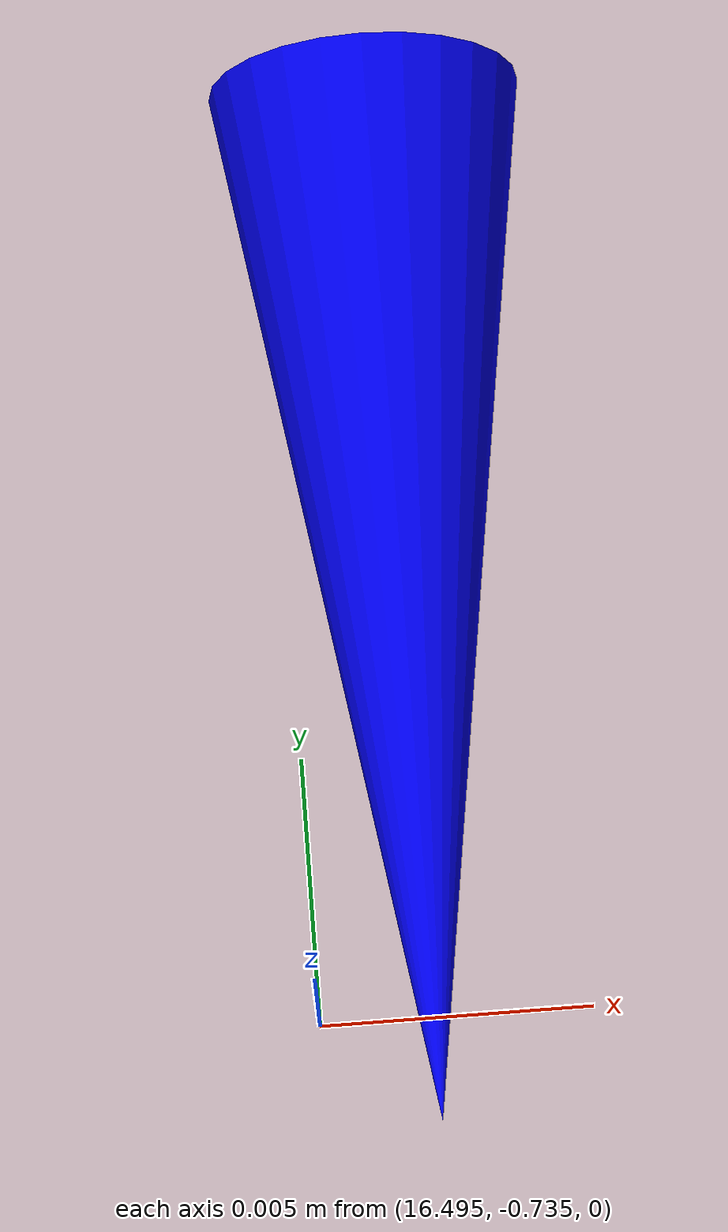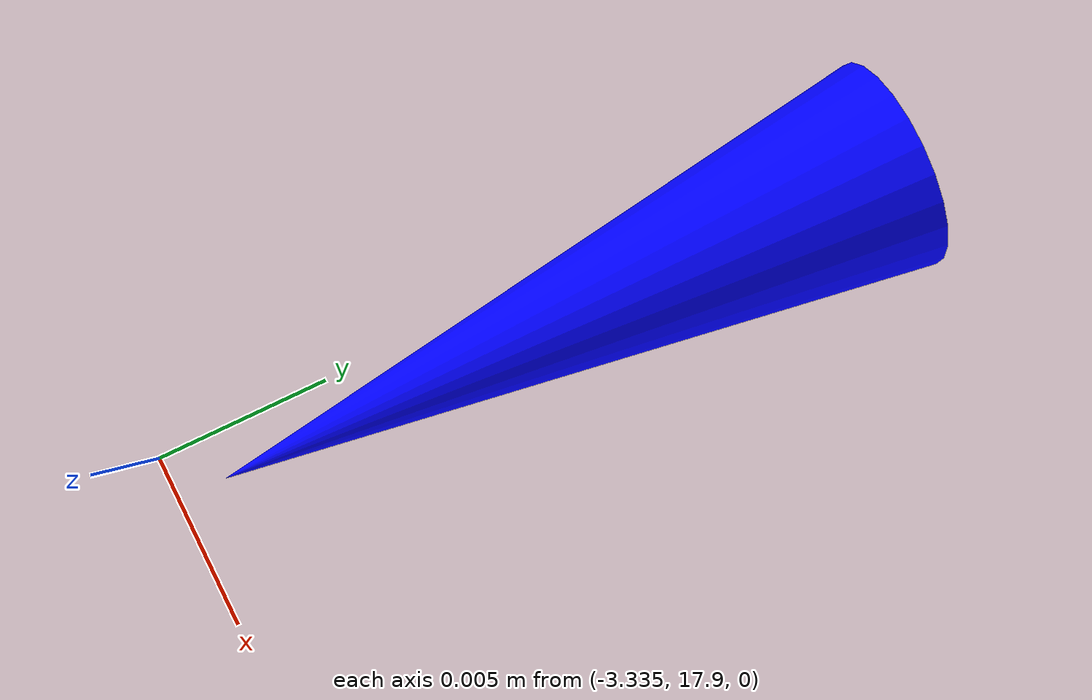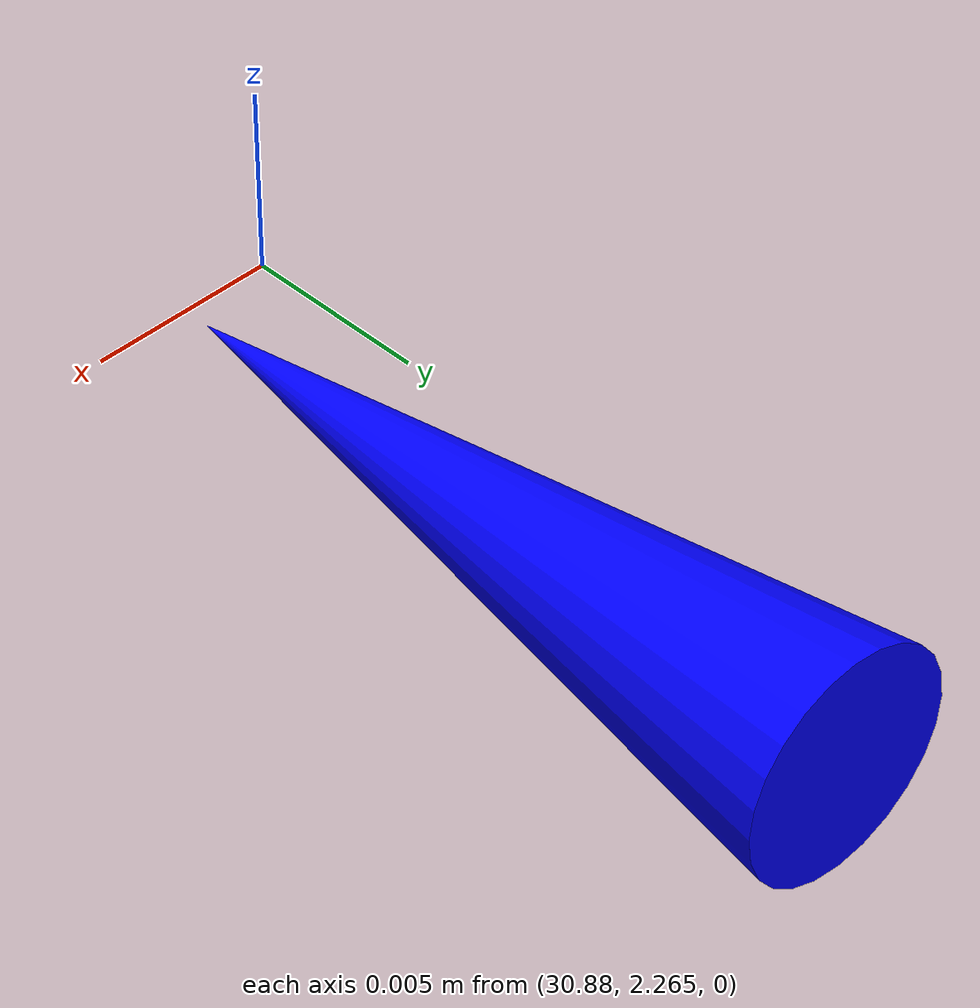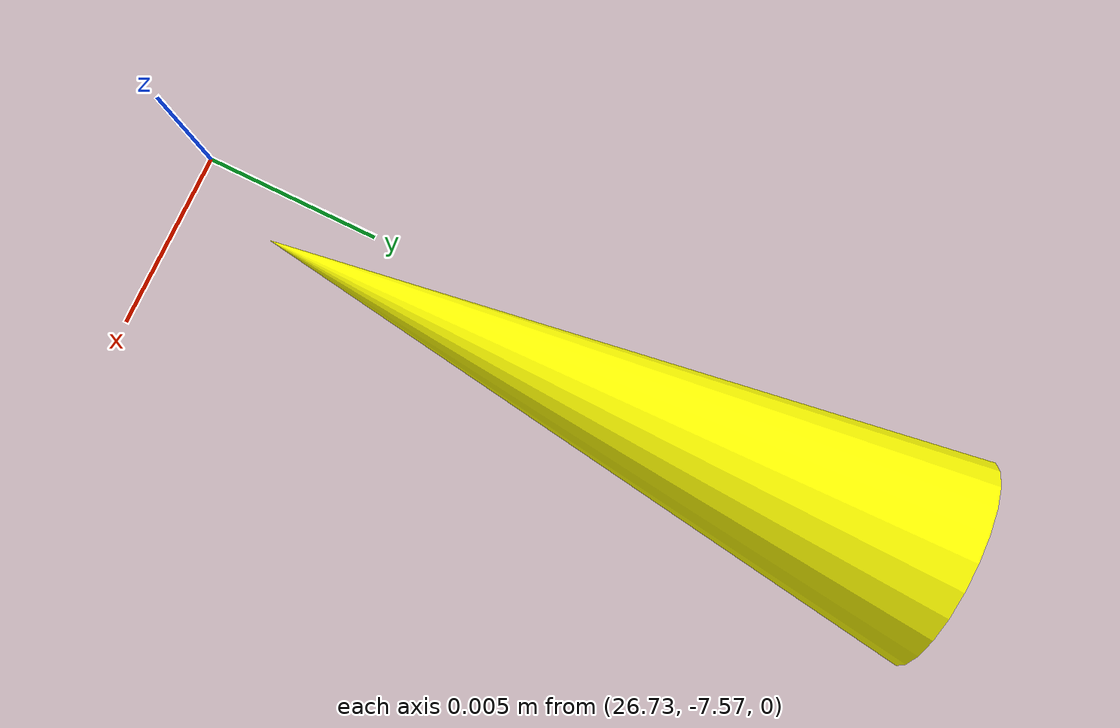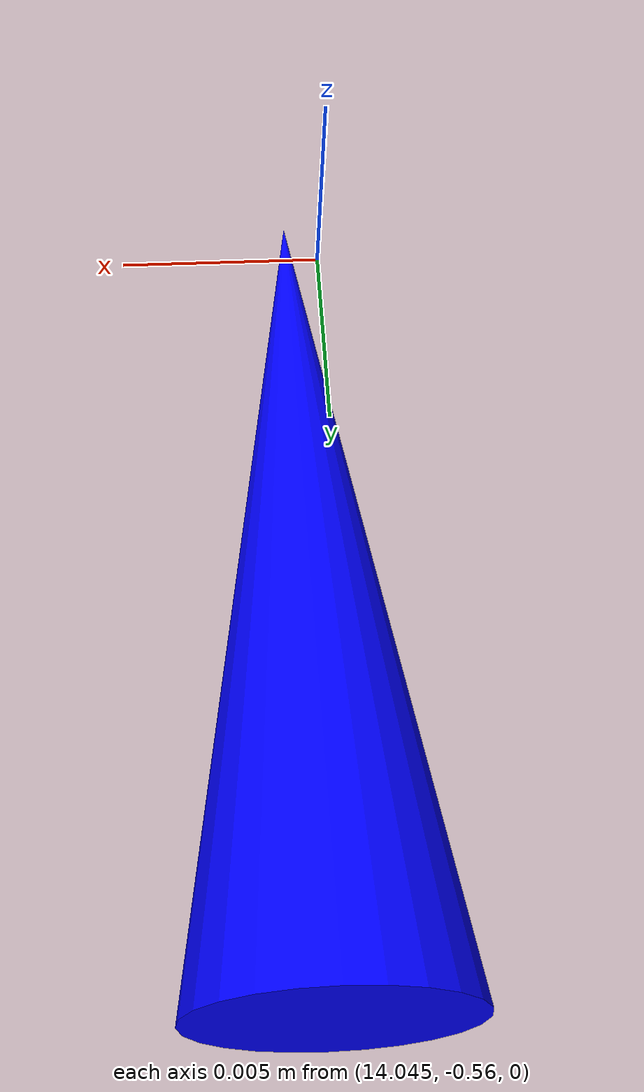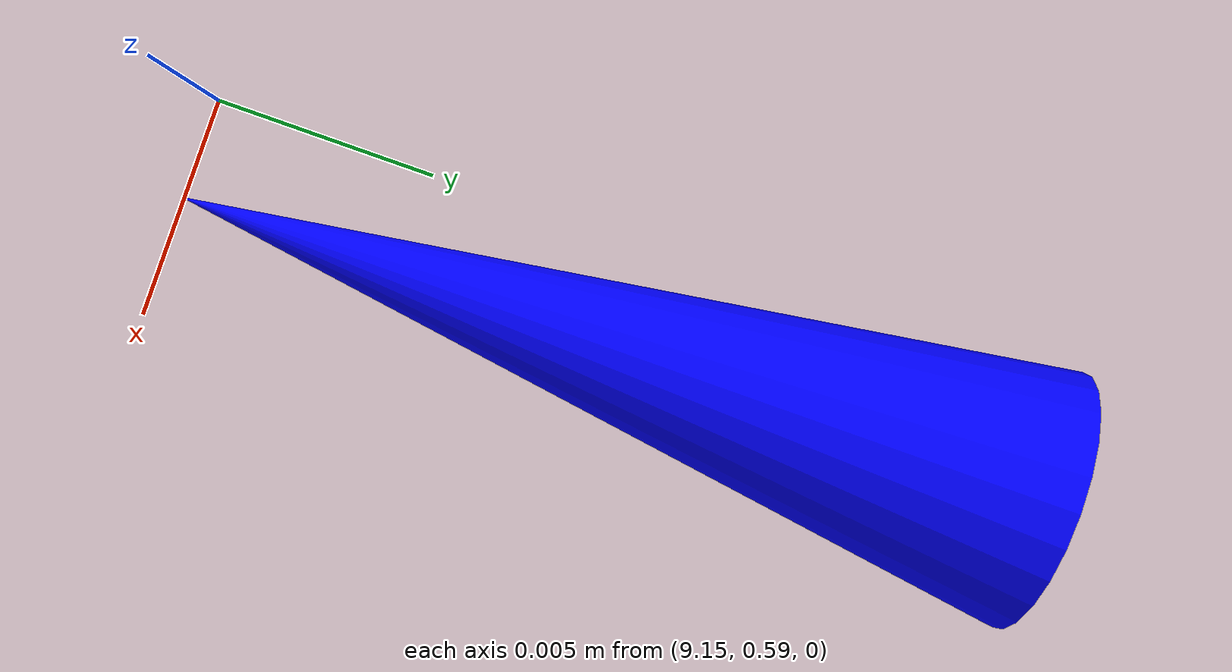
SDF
<?xml version="1.0"?>
  <sdf version='1.9'>
     <model name='cone_0'>
      <link name='cone_0_link'>
        <inertial>
			<mass>0</mass>
			<inertia>
			<ixx>0.166667</ixx>
			<ixy>0</ixy>
			<ixz>0</ixz>
			<iyy>0.166667</iyy>
			<iyz>0</iyz>
			<izz>0.166667</izz>
			</inertia>
		</inertial>
        <collision name='cone_0_collision'>
          <geometry>
            <mesh>
              <uri>/models/cone/meshes/cone.stl</uri>
              <scale>0.001 0.001 0.001</scale>
            </mesh>
          </geometry>
        </collision>
        <visual name='cone_0_visual'>
          <geometry>
            <mesh>
              <uri>/models/cone/meshes/cone.stl</uri>
              <scale>0.001 0.001 0.001</scale>
            </mesh>
          </geometry>
          <material>
            <ambient>1 1 0 1</ambient>
            <diffuse>1 1 0 1</diffuse>
            <specular>1 1 0 1</specular>
          </material>
        </visual>

        <enable_wind>false</enable_wind>
      </link>
      <pose>10.162562719662983 -6.805789525270462 0.0 1.57 0 0</pose>
      <static>true</static>
      </model>

     <model name='cone_1'>
      <link name='cone_1_link'>
        <inertial>
			<mass>0</mass>
			<inertia>
			<ixx>0.166667</ixx>
			<ixy>0</ixy>
			<ixz>0</ixz>
			<iyy>0.166667</iyy>
			<iyz>0</iyz>
			<izz>0.166667</izz>
			</inertia>
		</inertial>
        <collision name='cone_1_collision'>
          <geometry>
            <mesh>
              <uri>/models/cone/meshes/cone.stl</uri>
              <scale>0.001 0.001 0.001</scale>
            </mesh>
          </geometry>
        </collision>
        <visual name='cone_1_visual'>
          <geometry>
            <mesh>
              <uri>/models/cone/meshes/cone.stl</uri>
              <scale>0.001 0.001 0.001</scale>
            </mesh>
          </geometry>
          <material>
            <ambient>1 1 0 1</ambient>
            <diffuse>1 1 0 1</diffuse>
            <specular>1 1 0 1</specular>
          </material>
        </visual>

        <enable_wind>false</enable_wind>
      </link>
      <pose>12.795808569272358 -7.115429956674575 0.0 1.57 0 0</pose>
      <static>true</static>
      </model>

     <model name='cone_2'>
      <link name='cone_2_link'>
        <inertial>
			<mass>0</mass>
			<inertia>
			<ixx>0.166667</ixx>
			<ixy>0</ixy>
			<ixz>0</ixz>
			<iyy>0.166667</iyy>
			<iyz>0</iyz>
			<izz>0.166667</izz>
			</inertia>
		</inertial>
        <collision name='cone_2_collision'>
          <geometry>
            <mesh>
              <uri>/models/cone/meshes/cone.stl</uri>
              <scale>0.001 0.001 0.001</scale>
            </mesh>
          </geometry>
        </collision>
        <visual name='cone_2_visual'>
          <geometry>
            <mesh>
              <uri>/models/cone/meshes/cone.stl</uri>
              <scale>0.001 0.001 0.001</scale>
            </mesh>
          </geometry>
          <material>
            <ambient>1 1 0 1</ambient>
            <diffuse>1 1 0 1</diffuse>
            <specular>1 1 0 1</specular>
          </material>
        </visual>

        <enable_wind>false</enable_wind>
      </link>
      <pose>16.41324783929189 -7.453533823251724 0.0 1.57 0 0</pose>
      <static>true</static>
      </model>

     <model name='cone_3'>
      <link name='cone_3_link'>
        <inertial>
			<mass>0</mass>
			<inertia>
			<ixx>0.166667</ixx>
			<ixy>0</ixy>
			<ixz>0</ixz>
			<iyy>0.166667</iyy>
			<iyz>0</iyz>
			<izz>0.166667</izz>
			</inertia>
		</inertial>
        <collision name='cone_3_collision'>
          <geometry>
            <mesh>
              <uri>/models/cone/meshes/cone.stl</uri>
              <scale>0.001 0.001 0.001</scale>
            </mesh>
          </geometry>
        </collision>
        <visual name='cone_3_visual'>
          <geometry>
            <mesh>
              <uri>/models/cone/meshes/cone.stl</uri>
              <scale>0.001 0.001 0.001</scale>
            </mesh>
          </geometry>
          <material>
            <ambient>1 1 0 1</ambient>
            <diffuse>1 1 0 1</diffuse>
            <specular>1 1 0 1</specular>
          </material>
        </visual>

        <enable_wind>false</enable_wind>
      </link>
      <pose>18.394258467038473 -7.573309887409209 0.0 1.57 0 0</pose>
      <static>true</static>
      </model>

     <model name='cone_4'>
      <link name='cone_4_link'>
        <inertial>
			<mass>0</mass>
			<inertia>
			<ixx>0.166667</ixx>
			<ixy>0</ixy>
			<ixz>0</ixz>
			<iyy>0.166667</iyy>
			<iyz>0</iyz>
			<izz>0.166667</izz>
			</inertia>
		</inertial>
        <collision name='cone_4_collision'>
          <geometry>
            <mesh>
              <uri>/models/cone/meshes/cone.stl</uri>
              <scale>0.001 0.001 0.001</scale>
            </mesh>
          </geometry>
        </collision>
        <visual name='cone_4_visual'>
          <geometry>
            <mesh>
              <uri>/models/cone/meshes/cone.stl</uri>
              <scale>0.001 0.001 0.001</scale>
            </mesh>
          </geometry>
          <material>
            <ambient>1 1 0 1</ambient>
            <diffuse>1 1 0 1</diffuse>
            <specular>1 1 0 1</specular>
          </material>
        </visual>

        <enable_wind>false</enable_wind>
      </link>
      <pose>20.36416737206777 -7.697794399619101 0.0 1.57 0 0</pose>
      <static>true</static>
      </model>

     <model name='cone_5'>
      <link name='cone_5_link'>
        <inertial>
			<mass>0</mass>
			<inertia>
			<ixx>0.166667</ixx>
			<ixy>0</ixy>
			<ixz>0</ixz>
			<iyy>0.166667</iyy>
			<iyz>0</iyz>
			<izz>0.166667</izz>
			</inertia>
		</inertial>
        <collision name='cone_5_collision'>
          <geometry>
            <mesh>
              <uri>/models/cone/meshes/cone.stl</uri>
              <scale>0.001 0.001 0.001</scale>
            </mesh>
          </geometry>
        </collision>
        <visual name='cone_5_visual'>
          <geometry>
            <mesh>
              <uri>/models/cone/meshes/cone.stl</uri>
              <scale>0.001 0.001 0.001</scale>
            </mesh>
          </geometry>
          <material>
            <ambient>1 1 0 1</ambient>
            <diffuse>1 1 0 1</diffuse>
            <specular>1 1 0 1</specular>
          </material>
        </visual>

        <enable_wind>false</enable_wind>
      </link>
      <pose>22.201572576840718 -8.092417500376701 0.0 1.57 0 0</pose>
      <static>true</static>
      </model>

     <model name='cone_6'>
      <link name='cone_6_link'>
        <inertial>
			<mass>0</mass>
			<inertia>
			<ixx>0.166667</ixx>
			<ixy>0</ixy>
			<ixz>0</ixz>
			<iyy>0.166667</iyy>
			<iyz>0</iyz>
			<izz>0.166667</izz>
			</inertia>
		</inertial>
        <collision name='cone_6_collision'>
          <geometry>
            <mesh>
              <uri>/models/cone/meshes/cone.stl</uri>
              <scale>0.001 0.001 0.001</scale>
            </mesh>
          </geometry>
        </collision>
        <visual name='cone_6_visual'>
          <geometry>
            <mesh>
              <uri>/models/cone/meshes/cone.stl</uri>
              <scale>0.001 0.001 0.001</scale>
            </mesh>
          </geometry>
          <material>
            <ambient>1 1 0 1</ambient>
            <diffuse>1 1 0 1</diffuse>
            <specular>1 1 0 1</specular>
          </material>
        </visual>

        <enable_wind>false</enable_wind>
      </link>
      <pose>24.413639227231343 -8.666420311689375 0.0 1.57 0 0</pose>
      <static>true</static>
      </model>

     <model name='cone_7'>
      <link name='cone_7_link'>
        <inertial>
			<mass>0</mass>
			<inertia>
			<ixx>0.166667</ixx>
			<ixy>0</ixy>
			<ixz>0</ixz>
			<iyy>0.166667</iyy>
			<iyz>0</iyz>
			<izz>0.166667</izz>
			</inertia>
		</inertial>
        <collision name='cone_7_collision'>
          <geometry>
            <mesh>
              <uri>/models/cone/meshes/cone.stl</uri>
              <scale>0.001 0.001 0.001</scale>
            </mesh>
          </geometry>
        </collision>
        <visual name='cone_7_visual'>
          <geometry>
            <mesh>
              <uri>/models/cone/meshes/cone.stl</uri>
              <scale>0.001 0.001 0.001</scale>
            </mesh>
          </geometry>
          <material>
            <ambient>1 1 0 1</ambient>
            <diffuse>1 1 0 1</diffuse>
            <specular>1 1 0 1</specular>
          </material>
        </visual>

        <enable_wind>false</enable_wind>
      </link>
      <pose>26.731294409116106 -7.547542191505431 0.0 1.57 0 0</pose>
      <static>true</static>
      </model>

     <model name='cone_8'>
      <link name='cone_8_link'>
        <inertial>
			<mass>0</mass>
			<inertia>
			<ixx>0.166667</ixx>
			<ixy>0</ixy>
			<ixz>0</ixz>
			<iyy>0.166667</iyy>
			<iyz>0</iyz>
			<izz>0.166667</izz>
			</inertia>
		</inertial>
        <collision name='cone_8_collision'>
          <geometry>
            <mesh>
              <uri>/models/cone/meshes/cone.stl</uri>
              <scale>0.001 0.001 0.001</scale>
            </mesh>
          </geometry>
        </collision>
        <visual name='cone_8_visual'>
          <geometry>
            <mesh>
              <uri>/models/cone/meshes/cone.stl</uri>
              <scale>0.001 0.001 0.001</scale>
            </mesh>
          </geometry>
          <material>
            <ambient>1 1 0 1</ambient>
            <diffuse>1 1 0 1</diffuse>
            <specular>1 1 0 1</specular>
          </material>
        </visual>

        <enable_wind>false</enable_wind>
      </link>
      <pose>29.061665502866106 -6.409353549242019 0.0 1.57 0 0</pose>
      <static>true</static>
      </model>

     <model name='cone_9'>
      <link name='cone_9_link'>
        <inertial>
			<mass>0</mass>
			<inertia>
			<ixx>0.166667</ixx>
			<ixy>0</ixy>
			<ixz>0</ixz>
			<iyy>0.166667</iyy>
			<iyz>0</iyz>
			<izz>0.166667</izz>
			</inertia>
		</inertial>
        <collision name='cone_9_collision'>
          <geometry>
            <mesh>
              <uri>/models/cone/meshes/cone.stl</uri>
              <scale>0.001 0.001 0.001</scale>
            </mesh>
          </geometry>
        </collision>
        <visual name='cone_9_visual'>
          <geometry>
            <mesh>
              <uri>/models/cone/meshes/cone.stl</uri>
              <scale>0.001 0.001 0.001</scale>
            </mesh>
          </geometry>
          <material>
            <ambient>1 1 0 1</ambient>
            <diffuse>1 1 0 1</diffuse>
            <specular>1 1 0 1</specular>
          </material>
        </visual>

        <enable_wind>false</enable_wind>
      </link>
      <pose>30.695816389401752 -5.838621861696243 0.0 1.57 0 0</pose>
      <static>true</static>
      </model>

     <model name='cone_10'>
      <link name='cone_10_link'>
        <inertial>
			<mass>0</mass>
			<inertia>
			<ixx>0.166667</ixx>
			<ixy>0</ixy>
			<ixz>0</ixz>
			<iyy>0.166667</iyy>
			<iyz>0</iyz>
			<izz>0.166667</izz>
			</inertia>
		</inertial>
        <collision name='cone_10_collision'>
          <geometry>
            <mesh>
              <uri>/models/cone/meshes/cone.stl</uri>
              <scale>0.001 0.001 0.001</scale>
            </mesh>
          </geometry>
        </collision>
        <visual name='cone_10_visual'>
          <geometry>
            <mesh>
              <uri>/models/cone/meshes/cone.stl</uri>
              <scale>0.001 0.001 0.001</scale>
            </mesh>
          </geometry>
          <material>
            <ambient>1 1 0 1</ambient>
            <diffuse>1 1 0 1</diffuse>
            <specular>1 1 0 1</specular>
          </material>
        </visual>

        <enable_wind>false</enable_wind>
      </link>
      <pose>31.649776808102924 -5.348515517473221 0.0 1.57 0 0</pose>
      <static>true</static>
      </model>

     <model name='cone_11'>
      <link name='cone_11_link'>
        <inertial>
			<mass>0</mass>
			<inertia>
			<ixx>0.166667</ixx>
			<ixy>0</ixy>
			<ixz>0</ixz>
			<iyy>0.166667</iyy>
			<iyz>0</iyz>
			<izz>0.166667</izz>
			</inertia>
		</inertial>
        <collision name='cone_11_collision'>
          <geometry>
            <mesh>
              <uri>/models/cone/meshes/cone.stl</uri>
              <scale>0.001 0.001 0.001</scale>
            </mesh>
          </geometry>
        </collision>
        <visual name='cone_11_visual'>
          <geometry>
            <mesh>
              <uri>/models/cone/meshes/cone.stl</uri>
              <scale>0.001 0.001 0.001</scale>
            </mesh>
          </geometry>
          <material>
            <ambient>1 1 0 1</ambient>
            <diffuse>1 1 0 1</diffuse>
            <specular>1 1 0 1</specular>
          </material>
        </visual>

        <enable_wind>false</enable_wind>
      </link>
      <pose>32.07224041589101 -3.9580292532443995 0.0 1.57 0 0</pose>
      <static>true</static>
      </model>

     <model name='cone_12'>
      <link name='cone_12_link'>
        <inertial>
			<mass>0</mass>
			<inertia>
			<ixx>0.166667</ixx>
			<ixy>0</ixy>
			<ixz>0</ixz>
			<iyy>0.166667</iyy>
			<iyz>0</iyz>
			<izz>0.166667</izz>
			</inertia>
		</inertial>
        <collision name='cone_12_collision'>
          <geometry>
            <mesh>
              <uri>/models/cone/meshes/cone.stl</uri>
              <scale>0.001 0.001 0.001</scale>
            </mesh>
          </geometry>
        </collision>
        <visual name='cone_12_visual'>
          <geometry>
            <mesh>
              <uri>/models/cone/meshes/cone.stl</uri>
              <scale>0.001 0.001 0.001</scale>
            </mesh>
          </geometry>
          <material>
            <ambient>1 1 0 1</ambient>
            <diffuse>1 1 0 1</diffuse>
            <specular>1 1 0 1</specular>
          </material>
        </visual>

        <enable_wind>false</enable_wind>
      </link>
      <pose>32.02151829369863 -2.7639905760288235 0.0 1.57 0 0</pose>
      <static>true</static>
      </model>

     <model name='cone_13'>
      <link name='cone_13_link'>
        <inertial>
			<mass>0</mass>
			<inertia>
			<ixx>0.166667</ixx>
			<ixy>0</ixy>
			<ixz>0</ixz>
			<iyy>0.166667</iyy>
			<iyz>0</iyz>
			<izz>0.166667</izz>
			</inertia>
		</inertial>
        <collision name='cone_13_collision'>
          <geometry>
            <mesh>
              <uri>/models/cone/meshes/cone.stl</uri>
              <scale>0.001 0.001 0.001</scale>
            </mesh>
          </geometry>
        </collision>
        <visual name='cone_13_visual'>
          <geometry>
            <mesh>
              <uri>/models/cone/meshes/cone.stl</uri>
              <scale>0.001 0.001 0.001</scale>
            </mesh>
          </geometry>
          <material>
            <ambient>1 1 0 1</ambient>
            <diffuse>1 1 0 1</diffuse>
            <specular>1 1 0 1</specular>
          </material>
        </visual>

        <enable_wind>false</enable_wind>
      </link>
      <pose>31.0368255294164 -1.2759465048313139 0.0 1.57 0 0</pose>
      <static>true</static>
      </model>

     <model name='cone_14'>
      <link name='cone_14_link'>
        <inertial>
			<mass>0</mass>
			<inertia>
			<ixx>0.166667</ixx>
			<ixy>0</ixy>
			<ixz>0</ixz>
			<iyy>0.166667</iyy>
			<iyz>0</iyz>
			<izz>0.166667</izz>
			</inertia>
		</inertial>
        <collision name='cone_14_collision'>
          <geometry>
            <mesh>
              <uri>/models/cone/meshes/cone.stl</uri>
              <scale>0.001 0.001 0.001</scale>
            </mesh>
          </geometry>
        </collision>
        <visual name='cone_14_visual'>
          <geometry>
            <mesh>
              <uri>/models/cone/meshes/cone.stl</uri>
              <scale>0.001 0.001 0.001</scale>
            </mesh>
          </geometry>
          <material>
            <ambient>1 1 0 1</ambient>
            <diffuse>1 1 0 1</diffuse>
            <specular>1 1 0 1</specular>
          </material>
        </visual>

        <enable_wind>false</enable_wind>
      </link>
      <pose>28.961919561703997 -0.5280628988742826 0.0 1.57 0 0</pose>
      <static>true</static>
      </model>

     <model name='cone_15'>
      <link name='cone_15_link'>
        <inertial>
			<mass>0</mass>
			<inertia>
			<ixx>0.166667</ixx>
			<ixy>0</ixy>
			<ixz>0</ixz>
			<iyy>0.166667</iyy>
			<iyz>0</iyz>
			<izz>0.166667</izz>
			</inertia>
		</inertial>
        <collision name='cone_15_collision'>
          <geometry>
            <mesh>
              <uri>/models/cone/meshes/cone.stl</uri>
              <scale>0.001 0.001 0.001</scale>
            </mesh>
          </geometry>
        </collision>
        <visual name='cone_15_visual'>
          <geometry>
            <mesh>
              <uri>/models/cone/meshes/cone.stl</uri>
              <scale>0.001 0.001 0.001</scale>
            </mesh>
          </geometry>
          <material>
            <ambient>1 1 0 1</ambient>
            <diffuse>1 1 0 1</diffuse>
            <specular>1 1 0 1</specular>
          </material>
        </visual>

        <enable_wind>false</enable_wind>
      </link>
      <pose>25.877728811581928 -1.1531319448947903 0.0 1.57 0 0</pose>
      <static>true</static>
      </model>

     <model name='cone_16'>
      <link name='cone_16_link'>
        <inertial>
			<mass>0</mass>
			<inertia>
			<ixx>0.166667</ixx>
			<ixy>0</ixy>
			<ixz>0</ixz>
			<iyy>0.166667</iyy>
			<iyz>0</iyz>
			<izz>0.166667</izz>
			</inertia>
		</inertial>
        <collision name='cone_16_collision'>
          <geometry>
            <mesh>
              <uri>/models/cone/meshes/cone.stl</uri>
              <scale>0.001 0.001 0.001</scale>
            </mesh>
          </geometry>
        </collision>
        <visual name='cone_16_visual'>
          <geometry>
            <mesh>
              <uri>/models/cone/meshes/cone.stl</uri>
              <scale>0.001 0.001 0.001</scale>
            </mesh>
          </geometry>
          <material>
            <ambient>1 1 0 1</ambient>
            <diffuse>1 1 0 1</diffuse>
            <specular>1 1 0 1</specular>
          </material>
        </visual>

        <enable_wind>false</enable_wind>
      </link>
      <pose>23.32193066247304 -1.792493040323257 0.0 1.57 0 0</pose>
      <static>true</static>
      </model>

     <model name='cone_17'>
      <link name='cone_17_link'>
        <inertial>
			<mass>0</mass>
			<inertia>
			<ixx>0.166667</ixx>
			<ixy>0</ixy>
			<ixz>0</ixz>
			<iyy>0.166667</iyy>
			<iyz>0</iyz>
			<izz>0.166667</izz>
			</inertia>
		</inertial>
        <collision name='cone_17_collision'>
          <geometry>
            <mesh>
              <uri>/models/cone/meshes/cone.stl</uri>
              <scale>0.001 0.001 0.001</scale>
            </mesh>
          </geometry>
        </collision>
        <visual name='cone_17_visual'>
          <geometry>
            <mesh>
              <uri>/models/cone/meshes/cone.stl</uri>
              <scale>0.001 0.001 0.001</scale>
            </mesh>
          </geometry>
          <material>
            <ambient>1 1 0 1</ambient>
            <diffuse>1 1 0 1</diffuse>
            <specular>1 1 0 1</specular>
          </material>
        </visual>

        <enable_wind>false</enable_wind>
      </link>
      <pose>20.8338563597997 -2.4094681093692776 0.0 1.57 0 0</pose>
      <static>true</static>
      </model>

     <model name='cone_18'>
      <link name='cone_18_link'>
        <inertial>
			<mass>0</mass>
			<inertia>
			<ixx>0.166667</ixx>
			<ixy>0</ixy>
			<ixz>0</ixz>
			<iyy>0.166667</iyy>
			<iyz>0</iyz>
			<izz>0.166667</izz>
			</inertia>
		</inertial>
        <collision name='cone_18_collision'>
          <geometry>
            <mesh>
              <uri>/models/cone/meshes/cone.stl</uri>
              <scale>0.001 0.001 0.001</scale>
            </mesh>
          </geometry>
        </collision>
        <visual name='cone_18_visual'>
          <geometry>
            <mesh>
              <uri>/models/cone/meshes/cone.stl</uri>
              <scale>0.001 0.001 0.001</scale>
            </mesh>
          </geometry>
          <material>
            <ambient>1 1 0 1</ambient>
            <diffuse>1 1 0 1</diffuse>
            <specular>1 1 0 1</specular>
          </material>
        </visual>

        <enable_wind>false</enable_wind>
      </link>
      <pose>18.57289272912343 -2.970410854578018 0.0 1.57 0 0</pose>
      <static>true</static>
      </model>

     <model name='cone_19'>
      <link name='cone_19_link'>
        <inertial>
			<mass>0</mass>
			<inertia>
			<ixx>0.166667</ixx>
			<ixy>0</ixy>
			<ixz>0</ixz>
			<iyy>0.166667</iyy>
			<iyz>0</iyz>
			<izz>0.166667</izz>
			</inertia>
		</inertial>
        <collision name='cone_19_collision'>
          <geometry>
            <mesh>
              <uri>/models/cone/meshes/cone.stl</uri>
              <scale>0.001 0.001 0.001</scale>
            </mesh>
          </geometry>
        </collision>
        <visual name='cone_19_visual'>
          <geometry>
            <mesh>
              <uri>/models/cone/meshes/cone.stl</uri>
              <scale>0.001 0.001 0.001</scale>
            </mesh>
          </geometry>
          <material>
            <ambient>1 1 0 1</ambient>
            <diffuse>1 1 0 1</diffuse>
            <specular>1 1 0 1</specular>
          </material>
        </visual>

        <enable_wind>false</enable_wind>
      </link>
      <pose>16.117686334927875 -3.415607626199722 0.0 1.57 0 0</pose>
      <static>true</static>
      </model>

     <model name='cone_20'>
      <link name='cone_20_link'>
        <inertial>
			<mass>0</mass>
			<inertia>
			<ixx>0.166667</ixx>
			<ixy>0</ixy>
			<ixz>0</ixz>
			<iyy>0.166667</iyy>
			<iyz>0</iyz>
			<izz>0.166667</izz>
			</inertia>
		</inertial>
        <collision name='cone_20_collision'>
          <geometry>
            <mesh>
              <uri>/models/cone/meshes/cone.stl</uri>
              <scale>0.001 0.001 0.001</scale>
            </mesh>
          </geometry>
        </collision>
        <visual name='cone_20_visual'>
          <geometry>
            <mesh>
              <uri>/models/cone/meshes/cone.stl</uri>
              <scale>0.001 0.001 0.001</scale>
            </mesh>
          </geometry>
          <material>
            <ambient>1 1 0 1</ambient>
            <diffuse>1 1 0 1</diffuse>
            <specular>1 1 0 1</specular>
          </material>
        </visual>

        <enable_wind>false</enable_wind>
      </link>
      <pose>13.773777548154195 -3.4143639395236964 0.0 1.57 0 0</pose>
      <static>true</static>
      </model>

     <model name='cone_21'>
      <link name='cone_21_link'>
        <inertial>
			<mass>0</mass>
			<inertia>
			<ixx>0.166667</ixx>
			<ixy>0</ixy>
			<ixz>0</ixz>
			<iyy>0.166667</iyy>
			<iyz>0</iyz>
			<izz>0.166667</izz>
			</inertia>
		</inertial>
        <collision name='cone_21_collision'>
          <geometry>
            <mesh>
              <uri>/models/cone/meshes/cone.stl</uri>
              <scale>0.001 0.001 0.001</scale>
            </mesh>
          </geometry>
        </collision>
        <visual name='cone_21_visual'>
          <geometry>
            <mesh>
              <uri>/models/cone/meshes/cone.stl</uri>
              <scale>0.001 0.001 0.001</scale>
            </mesh>
          </geometry>
          <material>
            <ambient>1 1 0 1</ambient>
            <diffuse>1 1 0 1</diffuse>
            <specular>1 1 0 1</specular>
          </material>
        </visual>

        <enable_wind>false</enable_wind>
      </link>
      <pose>11.334431663831074 -2.920538217782974 0.0 1.57 0 0</pose>
      <static>true</static>
      </model>

     <model name='cone_22'>
      <link name='cone_22_link'>
        <inertial>
			<mass>0</mass>
			<inertia>
			<ixx>0.166667</ixx>
			<ixy>0</ixy>
			<ixz>0</ixz>
			<iyy>0.166667</iyy>
			<iyz>0</iyz>
			<izz>0.166667</izz>
			</inertia>
		</inertial>
        <collision name='cone_22_collision'>
          <geometry>
            <mesh>
              <uri>/models/cone/meshes/cone.stl</uri>
              <scale>0.001 0.001 0.001</scale>
            </mesh>
          </geometry>
        </collision>
        <visual name='cone_22_visual'>
          <geometry>
            <mesh>
              <uri>/models/cone/meshes/cone.stl</uri>
              <scale>0.001 0.001 0.001</scale>
            </mesh>
          </geometry>
          <material>
            <ambient>1 1 0 1</ambient>
            <diffuse>1 1 0 1</diffuse>
            <specular>1 1 0 1</specular>
          </material>
        </visual>

        <enable_wind>false</enable_wind>
      </link>
      <pose>9.351900974591572 -2.528150064706802 0.0 1.57 0 0</pose>
      <static>true</static>
      </model>

     <model name='cone_23'>
      <link name='cone_23_link'>
        <inertial>
			<mass>0</mass>
			<inertia>
			<ixx>0.166667</ixx>
			<ixy>0</ixy>
			<ixz>0</ixz>
			<iyy>0.166667</iyy>
			<iyz>0</iyz>
			<izz>0.166667</izz>
			</inertia>
		</inertial>
        <collision name='cone_23_collision'>
          <geometry>
            <mesh>
              <uri>/models/cone/meshes/cone.stl</uri>
              <scale>0.001 0.001 0.001</scale>
            </mesh>
          </geometry>
        </collision>
        <visual name='cone_23_visual'>
          <geometry>
            <mesh>
              <uri>/models/cone/meshes/cone.stl</uri>
              <scale>0.001 0.001 0.001</scale>
            </mesh>
          </geometry>
          <material>
            <ambient>1 1 0 1</ambient>
            <diffuse>1 1 0 1</diffuse>
            <specular>1 1 0 1</specular>
          </material>
        </visual>

        <enable_wind>false</enable_wind>
      </link>
      <pose>7.4034452474912005 -1.9263812849521633 0.0 1.57 0 0</pose>
      <static>true</static>
      </model>

     <model name='cone_24'>
      <link name='cone_24_link'>
        <inertial>
			<mass>0</mass>
			<inertia>
			<ixx>0.166667</ixx>
			<ixy>0</ixy>
			<ixz>0</ixz>
			<iyy>0.166667</iyy>
			<iyz>0</iyz>
			<izz>0.166667</izz>
			</inertia>
		</inertial>
        <collision name='cone_24_collision'>
          <geometry>
            <mesh>
              <uri>/models/cone/meshes/cone.stl</uri>
              <scale>0.001 0.001 0.001</scale>
            </mesh>
          </geometry>
        </collision>
        <visual name='cone_24_visual'>
          <geometry>
            <mesh>
              <uri>/models/cone/meshes/cone.stl</uri>
              <scale>0.001 0.001 0.001</scale>
            </mesh>
          </geometry>
          <material>
            <ambient>1 1 0 1</ambient>
            <diffuse>1 1 0 1</diffuse>
            <specular>1 1 0 1</specular>
          </material>
        </visual>

        <enable_wind>false</enable_wind>
      </link>
      <pose>5.362857571919759 -1.2730151960849758 0.0 1.57 0 0</pose>
      <static>true</static>
      </model>

     <model name='cone_25'>
      <link name='cone_25_link'>
        <inertial>
			<mass>0</mass>
			<inertia>
			<ixx>0.166667</ixx>
			<ixy>0</ixy>
			<ixz>0</ixz>
			<iyy>0.166667</iyy>
			<iyz>0</iyz>
			<izz>0.166667</izz>
			</inertia>
		</inertial>
        <collision name='cone_25_collision'>
          <geometry>
            <mesh>
              <uri>/models/cone/meshes/cone.stl</uri>
              <scale>0.001 0.001 0.001</scale>
            </mesh>
          </geometry>
        </collision>
        <visual name='cone_25_visual'>
          <geometry>
            <mesh>
              <uri>/models/cone/meshes/cone.stl</uri>
              <scale>0.001 0.001 0.001</scale>
            </mesh>
          </geometry>
          <material>
            <ambient>1 1 0 1</ambient>
            <diffuse>1 1 0 1</diffuse>
            <specular>1 1 0 1</specular>
          </material>
        </visual>

        <enable_wind>false</enable_wind>
      </link>
      <pose>3.879997364362081 -0.25574892258644083 0.0 1.57 0 0</pose>
      <static>true</static>
      </model>

     <model name='cone_26'>
      <link name='cone_26_link'>
        <inertial>
			<mass>0</mass>
			<inertia>
			<ixx>0.166667</ixx>
			<ixy>0</ixy>
			<ixz>0</ixz>
			<iyy>0.166667</iyy>
			<iyz>0</iyz>
			<izz>0.166667</izz>
			</inertia>
		</inertial>
        <collision name='cone_26_collision'>
          <geometry>
            <mesh>
              <uri>/models/cone/meshes/cone.stl</uri>
              <scale>0.001 0.001 0.001</scale>
            </mesh>
          </geometry>
        </collision>
        <visual name='cone_26_visual'>
          <geometry>
            <mesh>
              <uri>/models/cone/meshes/cone.stl</uri>
              <scale>0.001 0.001 0.001</scale>
            </mesh>
          </geometry>
          <material>
            <ambient>1 1 0 1</ambient>
            <diffuse>1 1 0 1</diffuse>
            <specular>1 1 0 1</specular>
          </material>
        </visual>

        <enable_wind>false</enable_wind>
      </link>
      <pose>2.161596218427022 1.169443242788315 0.0 1.57 0 0</pose>
      <static>true</static>
      </model>

     <model name='cone_27'>
      <link name='cone_27_link'>
        <inertial>
			<mass>0</mass>
			<inertia>
			<ixx>0.166667</ixx>
			<ixy>0</ixy>
			<ixz>0</ixz>
			<iyy>0.166667</iyy>
			<iyz>0</iyz>
			<izz>0.166667</izz>
			</inertia>
		</inertial>
        <collision name='cone_27_collision'>
          <geometry>
            <mesh>
              <uri>/models/cone/meshes/cone.stl</uri>
              <scale>0.001 0.001 0.001</scale>
            </mesh>
          </geometry>
        </collision>
        <visual name='cone_27_visual'>
          <geometry>
            <mesh>
              <uri>/models/cone/meshes/cone.stl</uri>
              <scale>0.001 0.001 0.001</scale>
            </mesh>
          </geometry>
          <material>
            <ambient>1 1 0 1</ambient>
            <diffuse>1 1 0 1</diffuse>
            <specular>1 1 0 1</specular>
          </material>
        </visual>

        <enable_wind>false</enable_wind>
      </link>
      <pose>0.18256594308217372 2.740736215353012 0.0 1.57 0 0</pose>
      <static>true</static>
      </model>

     <model name='cone_28'>
      <link name='cone_28_link'>
        <inertial>
			<mass>0</mass>
			<inertia>
			<ixx>0.166667</ixx>
			<ixy>0</ixy>
			<ixz>0</ixz>
			<iyy>0.166667</iyy>
			<iyz>0</iyz>
			<izz>0.166667</izz>
			</inertia>
		</inertial>
        <collision name='cone_28_collision'>
          <geometry>
            <mesh>
              <uri>/models/cone/meshes/cone.stl</uri>
              <scale>0.001 0.001 0.001</scale>
            </mesh>
          </geometry>
        </collision>
        <visual name='cone_28_visual'>
          <geometry>
            <mesh>
              <uri>/models/cone/meshes/cone.stl</uri>
              <scale>0.001 0.001 0.001</scale>
            </mesh>
          </geometry>
          <material>
            <ambient>1 1 0 1</ambient>
            <diffuse>1 1 0 1</diffuse>
            <specular>1 1 0 1</specular>
          </material>
        </visual>

        <enable_wind>false</enable_wind>
      </link>
      <pose>-0.9314361893335977 4.719185369253158 0.0 1.57 0 0</pose>
      <static>true</static>
      </model>

     <model name='cone_29'>
      <link name='cone_29_link'>
        <inertial>
			<mass>0</mass>
			<inertia>
			<ixx>0.166667</ixx>
			<ixy>0</ixy>
			<ixz>0</ixz>
			<iyy>0.166667</iyy>
			<iyz>0</iyz>
			<izz>0.166667</izz>
			</inertia>
		</inertial>
        <collision name='cone_29_collision'>
          <geometry>
            <mesh>
              <uri>/models/cone/meshes/cone.stl</uri>
              <scale>0.001 0.001 0.001</scale>
            </mesh>
          </geometry>
        </collision>
        <visual name='cone_29_visual'>
          <geometry>
            <mesh>
              <uri>/models/cone/meshes/cone.stl</uri>
              <scale>0.001 0.001 0.001</scale>
            </mesh>
          </geometry>
          <material>
            <ambient>1 1 0 1</ambient>
            <diffuse>1 1 0 1</diffuse>
            <specular>1 1 0 1</specular>
          </material>
        </visual>

        <enable_wind>false</enable_wind>
      </link>
      <pose>-2.1149632774988807 6.792155378103256 0.0 1.57 0 0</pose>
      <static>true</static>
      </model>

     <model name='cone_30'>
      <link name='cone_30_link'>
        <inertial>
			<mass>0</mass>
			<inertia>
			<ixx>0.166667</ixx>
			<ixy>0</ixy>
			<ixz>0</ixz>
			<iyy>0.166667</iyy>
			<iyz>0</iyz>
			<izz>0.166667</izz>
			</inertia>
		</inertial>
        <collision name='cone_30_collision'>
          <geometry>
            <mesh>
              <uri>/models/cone/meshes/cone.stl</uri>
              <scale>0.001 0.001 0.001</scale>
            </mesh>
          </geometry>
        </collision>
        <visual name='cone_30_visual'>
          <geometry>
            <mesh>
              <uri>/models/cone/meshes/cone.stl</uri>
              <scale>0.001 0.001 0.001</scale>
            </mesh>
          </geometry>
          <material>
            <ambient>1 1 0 1</ambient>
            <diffuse>1 1 0 1</diffuse>
            <specular>1 1 0 1</specular>
          </material>
        </visual>

        <enable_wind>false</enable_wind>
      </link>
      <pose>-3.200211080233256 8.680440252065658 0.0 1.57 0 0</pose>
      <static>true</static>
      </model>

     <model name='cone_31'>
      <link name='cone_31_link'>
        <inertial>
			<mass>0</mass>
			<inertia>
			<ixx>0.166667</ixx>
			<ixy>0</ixy>
			<ixz>0</ixz>
			<iyy>0.166667</iyy>
			<iyz>0</iyz>
			<izz>0.166667</izz>
			</inertia>
		</inertial>
        <collision name='cone_31_collision'>
          <geometry>
            <mesh>
              <uri>/models/cone/meshes/cone.stl</uri>
              <scale>0.001 0.001 0.001</scale>
            </mesh>
          </geometry>
        </collision>
        <visual name='cone_31_visual'>
          <geometry>
            <mesh>
              <uri>/models/cone/meshes/cone.stl</uri>
              <scale>0.001 0.001 0.001</scale>
            </mesh>
          </geometry>
          <material>
            <ambient>1 1 0 1</ambient>
            <diffuse>1 1 0 1</diffuse>
            <specular>1 1 0 1</specular>
          </material>
        </visual>

        <enable_wind>false</enable_wind>
      </link>
      <pose>-4.171241315523783 10.601599042654037 0.0 1.57 0 0</pose>
      <static>true</static>
      </model>

     <model name='cone_32'>
      <link name='cone_32_link'>
        <inertial>
			<mass>0</mass>
			<inertia>
			<ixx>0.166667</ixx>
			<ixy>0</ixy>
			<ixz>0</ixz>
			<iyy>0.166667</iyy>
			<iyz>0</iyz>
			<izz>0.166667</izz>
			</inertia>
		</inertial>
        <collision name='cone_32_collision'>
          <geometry>
            <mesh>
              <uri>/models/cone/meshes/cone.stl</uri>
              <scale>0.001 0.001 0.001</scale>
            </mesh>
          </geometry>
        </collision>
        <visual name='cone_32_visual'>
          <geometry>
            <mesh>
              <uri>/models/cone/meshes/cone.stl</uri>
              <scale>0.001 0.001 0.001</scale>
            </mesh>
          </geometry>
          <material>
            <ambient>1 1 0 1</ambient>
            <diffuse>1 1 0 1</diffuse>
            <specular>1 1 0 1</specular>
          </material>
        </visual>

        <enable_wind>false</enable_wind>
      </link>
      <pose>-4.655250390688578 12.802849691152572 0.0 1.57 0 0</pose>
      <static>true</static>
      </model>

     <model name='cone_33'>
      <link name='cone_33_link'>
        <inertial>
			<mass>0</mass>
			<inertia>
			<ixx>0.166667</ixx>
			<ixy>0</ixy>
			<ixz>0</ixz>
			<iyy>0.166667</iyy>
			<iyz>0</iyz>
			<izz>0.166667</izz>
			</inertia>
		</inertial>
        <collision name='cone_33_collision'>
          <geometry>
            <mesh>
              <uri>/models/cone/meshes/cone.stl</uri>
              <scale>0.001 0.001 0.001</scale>
            </mesh>
          </geometry>
        </collision>
        <visual name='cone_33_visual'>
          <geometry>
            <mesh>
              <uri>/models/cone/meshes/cone.stl</uri>
              <scale>0.001 0.001 0.001</scale>
            </mesh>
          </geometry>
          <material>
            <ambient>1 1 0 1</ambient>
            <diffuse>1 1 0 1</diffuse>
            <specular>1 1 0 1</specular>
          </material>
        </visual>

        <enable_wind>false</enable_wind>
      </link>
      <pose>-5.336643823305765 14.762333791494369 0.0 1.57 0 0</pose>
      <static>true</static>
      </model>

     <model name='cone_34'>
      <link name='cone_34_link'>
        <inertial>
			<mass>0</mass>
			<inertia>
			<ixx>0.166667</ixx>
			<ixy>0</ixy>
			<ixz>0</ixz>
			<iyy>0.166667</iyy>
			<iyz>0</iyz>
			<izz>0.166667</izz>
			</inertia>
		</inertial>
        <collision name='cone_34_collision'>
          <geometry>
            <mesh>
              <uri>/models/cone/meshes/cone.stl</uri>
              <scale>0.001 0.001 0.001</scale>
            </mesh>
          </geometry>
        </collision>
        <visual name='cone_34_visual'>
          <geometry>
            <mesh>
              <uri>/models/cone/meshes/cone.stl</uri>
              <scale>0.001 0.001 0.001</scale>
            </mesh>
          </geometry>
          <material>
            <ambient>1 1 0 1</ambient>
            <diffuse>1 1 0 1</diffuse>
            <specular>1 1 0 1</specular>
          </material>
        </visual>

        <enable_wind>false</enable_wind>
      </link>
      <pose>-6.324036248842875 16.59299785399437 0.0 1.57 0 0</pose>
      <static>true</static>
      </model>

     <model name='cone_35'>
      <link name='cone_35_link'>
        <inertial>
			<mass>0</mass>
			<inertia>
			<ixx>0.166667</ixx>
			<ixy>0</ixy>
			<ixz>0</ixz>
			<iyy>0.166667</iyy>
			<iyz>0</iyz>
			<izz>0.166667</izz>
			</inertia>
		</inertial>
        <collision name='cone_35_collision'>
          <geometry>
            <mesh>
              <uri>/models/cone/meshes/cone.stl</uri>
              <scale>0.001 0.001 0.001</scale>
            </mesh>
          </geometry>
        </collision>
        <visual name='cone_35_visual'>
          <geometry>
            <mesh>
              <uri>/models/cone/meshes/cone.stl</uri>
              <scale>0.001 0.001 0.001</scale>
            </mesh>
          </geometry>
          <material>
            <ambient>1 1 0 1</ambient>
            <diffuse>1 1 0 1</diffuse>
            <specular>1 1 0 1</specular>
          </material>
        </visual>

        <enable_wind>false</enable_wind>
      </link>
      <pose>-8.037167581240336 18.12053348326683 0.0 1.57 0 0</pose>
      <static>true</static>
      </model>

     <model name='cone_36'>
      <link name='cone_36_link'>
        <inertial>
			<mass>0</mass>
			<inertia>
			<ixx>0.166667</ixx>
			<ixy>0</ixy>
			<ixz>0</ixz>
			<iyy>0.166667</iyy>
			<iyz>0</iyz>
			<izz>0.166667</izz>
			</inertia>
		</inertial>
        <collision name='cone_36_collision'>
          <geometry>
            <mesh>
              <uri>/models/cone/meshes/cone.stl</uri>
              <scale>0.001 0.001 0.001</scale>
            </mesh>
          </geometry>
        </collision>
        <visual name='cone_36_visual'>
          <geometry>
            <mesh>
              <uri>/models/cone/meshes/cone.stl</uri>
              <scale>0.001 0.001 0.001</scale>
            </mesh>
          </geometry>
          <material>
            <ambient>1 1 0 1</ambient>
            <diffuse>1 1 0 1</diffuse>
            <specular>1 1 0 1</specular>
          </material>
        </visual>

        <enable_wind>false</enable_wind>
      </link>
      <pose>-9.63115733496348 17.907305639028547 0.0 1.57 0 0</pose>
      <static>true</static>
      </model>

     <model name='cone_37'>
      <link name='cone_37_link'>
        <inertial>
			<mass>0</mass>
			<inertia>
			<ixx>0.166667</ixx>
			<ixy>0</ixy>
			<ixz>0</ixz>
			<iyy>0.166667</iyy>
			<iyz>0</iyz>
			<izz>0.166667</izz>
			</inertia>
		</inertial>
        <collision name='cone_37_collision'>
          <geometry>
            <mesh>
              <uri>/models/cone/meshes/cone.stl</uri>
              <scale>0.001 0.001 0.001</scale>
            </mesh>
          </geometry>
        </collision>
        <visual name='cone_37_visual'>
          <geometry>
            <mesh>
              <uri>/models/cone/meshes/cone.stl</uri>
              <scale>0.001 0.001 0.001</scale>
            </mesh>
          </geometry>
          <material>
            <ambient>1 1 0 1</ambient>
            <diffuse>1 1 0 1</diffuse>
            <specular>1 1 0 1</specular>
          </material>
        </visual>

        <enable_wind>false</enable_wind>
      </link>
      <pose>-11.459885438601175 17.15815631651878 0.0 1.57 0 0</pose>
      <static>true</static>
      </model>

     <model name='cone_38'>
      <link name='cone_38_link'>
        <inertial>
			<mass>0</mass>
			<inertia>
			<ixx>0.166667</ixx>
			<ixy>0</ixy>
			<ixz>0</ixz>
			<iyy>0.166667</iyy>
			<iyz>0</iyz>
			<izz>0.166667</izz>
			</inertia>
		</inertial>
        <collision name='cone_38_collision'>
          <geometry>
            <mesh>
              <uri>/models/cone/meshes/cone.stl</uri>
              <scale>0.001 0.001 0.001</scale>
            </mesh>
          </geometry>
        </collision>
        <visual name='cone_38_visual'>
          <geometry>
            <mesh>
              <uri>/models/cone/meshes/cone.stl</uri>
              <scale>0.001 0.001 0.001</scale>
            </mesh>
          </geometry>
          <material>
            <ambient>1 1 0 1</ambient>
            <diffuse>1 1 0 1</diffuse>
            <specular>1 1 0 1</specular>
          </material>
        </visual>

        <enable_wind>false</enable_wind>
      </link>
      <pose>-13.498888047854106 15.954734914541243 0.0 1.57 0 0</pose>
      <static>true</static>
      </model>

     <model name='cone_39'>
      <link name='cone_39_link'>
        <inertial>
			<mass>0</mass>
			<inertia>
			<ixx>0.166667</ixx>
			<ixy>0</ixy>
			<ixz>0</ixz>
			<iyy>0.166667</iyy>
			<iyz>0</iyz>
			<izz>0.166667</izz>
			</inertia>
		</inertial>
        <collision name='cone_39_collision'>
          <geometry>
            <mesh>
              <uri>/models/cone/meshes/cone.stl</uri>
              <scale>0.001 0.001 0.001</scale>
            </mesh>
          </geometry>
        </collision>
        <visual name='cone_39_visual'>
          <geometry>
            <mesh>
              <uri>/models/cone/meshes/cone.stl</uri>
              <scale>0.001 0.001 0.001</scale>
            </mesh>
          </geometry>
          <material>
            <ambient>1 1 0 1</ambient>
            <diffuse>1 1 0 1</diffuse>
            <specular>1 1 0 1</specular>
          </material>
        </visual>

        <enable_wind>false</enable_wind>
      </link>
      <pose>-15.432049783388772 14.461224096059798 0.0 1.57 0 0</pose>
      <static>true</static>
      </model>

     <model name='cone_40'>
      <link name='cone_40_link'>
        <inertial>
			<mass>0</mass>
			<inertia>
			<ixx>0.166667</ixx>
			<ixy>0</ixy>
			<ixz>0</ixz>
			<iyy>0.166667</iyy>
			<iyz>0</iyz>
			<izz>0.166667</izz>
			</inertia>
		</inertial>
        <collision name='cone_40_collision'>
          <geometry>
            <mesh>
              <uri>/models/cone/meshes/cone.stl</uri>
              <scale>0.001 0.001 0.001</scale>
            </mesh>
          </geometry>
        </collision>
        <visual name='cone_40_visual'>
          <geometry>
            <mesh>
              <uri>/models/cone/meshes/cone.stl</uri>
              <scale>0.001 0.001 0.001</scale>
            </mesh>
          </geometry>
          <material>
            <ambient>1 1 0 1</ambient>
            <diffuse>1 1 0 1</diffuse>
            <specular>1 1 0 1</specular>
          </material>
        </visual>

        <enable_wind>false</enable_wind>
      </link>
      <pose>-17.52772792212168 13.083641164541245 0.0 1.57 0 0</pose>
      <static>true</static>
      </model>

     <model name='cone_41'>
      <link name='cone_41_link'>
        <inertial>
			<mass>0</mass>
			<inertia>
			<ixx>0.166667</ixx>
			<ixy>0</ixy>
			<ixz>0</ixz>
			<iyy>0.166667</iyy>
			<iyz>0</iyz>
			<izz>0.166667</izz>
			</inertia>
		</inertial>
        <collision name='cone_41_collision'>
          <geometry>
            <mesh>
              <uri>/models/cone/meshes/cone.stl</uri>
              <scale>0.001 0.001 0.001</scale>
            </mesh>
          </geometry>
        </collision>
        <visual name='cone_41_visual'>
          <geometry>
            <mesh>
              <uri>/models/cone/meshes/cone.stl</uri>
              <scale>0.001 0.001 0.001</scale>
            </mesh>
          </geometry>
          <material>
            <ambient>1 1 0 1</ambient>
            <diffuse>1 1 0 1</diffuse>
            <specular>1 1 0 1</specular>
          </material>
        </visual>

        <enable_wind>false</enable_wind>
      </link>
      <pose>-19.55779307715098 11.692100637197495 0.0 1.57 0 0</pose>
      <static>true</static>
      </model>

     <model name='cone_42'>
      <link name='cone_42_link'>
        <inertial>
			<mass>0</mass>
			<inertia>
			<ixx>0.166667</ixx>
			<ixy>0</ixy>
			<ixz>0</ixz>
			<iyy>0.166667</iyy>
			<iyz>0</iyz>
			<izz>0.166667</izz>
			</inertia>
		</inertial>
        <collision name='cone_42_collision'>
          <geometry>
            <mesh>
              <uri>/models/cone/meshes/cone.stl</uri>
              <scale>0.001 0.001 0.001</scale>
            </mesh>
          </geometry>
        </collision>
        <visual name='cone_42_visual'>
          <geometry>
            <mesh>
              <uri>/models/cone/meshes/cone.stl</uri>
              <scale>0.001 0.001 0.001</scale>
            </mesh>
          </geometry>
          <material>
            <ambient>1 1 0 1</ambient>
            <diffuse>1 1 0 1</diffuse>
            <specular>1 1 0 1</specular>
          </material>
        </visual>

        <enable_wind>false</enable_wind>
      </link>
      <pose>-21.78338206640879 10.063402478933334 0.0 1.57 0 0</pose>
      <static>true</static>
      </model>

     <model name='cone_43'>
      <link name='cone_43_link'>
        <inertial>
			<mass>0</mass>
			<inertia>
			<ixx>0.166667</ixx>
			<ixy>0</ixy>
			<ixz>0</ixz>
			<iyy>0.166667</iyy>
			<iyz>0</iyz>
			<izz>0.166667</izz>
			</inertia>
		</inertial>
        <collision name='cone_43_collision'>
          <geometry>
            <mesh>
              <uri>/models/cone/meshes/cone.stl</uri>
              <scale>0.001 0.001 0.001</scale>
            </mesh>
          </geometry>
        </collision>
        <visual name='cone_43_visual'>
          <geometry>
            <mesh>
              <uri>/models/cone/meshes/cone.stl</uri>
              <scale>0.001 0.001 0.001</scale>
            </mesh>
          </geometry>
          <material>
            <ambient>1 1 0 1</ambient>
            <diffuse>1 1 0 1</diffuse>
            <specular>1 1 0 1</specular>
          </material>
        </visual>

        <enable_wind>false</enable_wind>
      </link>
      <pose>-24.116009553591407 8.587853353261947 0.0 1.57 0 0</pose>
      <static>true</static>
      </model>

     <model name='cone_44'>
      <link name='cone_44_link'>
        <inertial>
			<mass>0</mass>
			<inertia>
			<ixx>0.166667</ixx>
			<ixy>0</ixy>
			<ixz>0</ixz>
			<iyy>0.166667</iyy>
			<iyz>0</iyz>
			<izz>0.166667</izz>
			</inertia>
		</inertial>
        <collision name='cone_44_collision'>
          <geometry>
            <mesh>
              <uri>/models/cone/meshes/cone.stl</uri>
              <scale>0.001 0.001 0.001</scale>
            </mesh>
          </geometry>
        </collision>
        <visual name='cone_44_visual'>
          <geometry>
            <mesh>
              <uri>/models/cone/meshes/cone.stl</uri>
              <scale>0.001 0.001 0.001</scale>
            </mesh>
          </geometry>
          <material>
            <ambient>1 1 0 1</ambient>
            <diffuse>1 1 0 1</diffuse>
            <specular>1 1 0 1</specular>
          </material>
        </visual>

        <enable_wind>false</enable_wind>
      </link>
      <pose>-25.488123735109962 7.439182203054428 0.0 1.57 0 0</pose>
      <static>true</static>
      </model>

     <model name='cone_45'>
      <link name='cone_45_link'>
        <inertial>
			<mass>0</mass>
			<inertia>
			<ixx>0.166667</ixx>
			<ixy>0</ixy>
			<ixz>0</ixz>
			<iyy>0.166667</iyy>
			<iyz>0</iyz>
			<izz>0.166667</izz>
			</inertia>
		</inertial>
        <collision name='cone_45_collision'>
          <geometry>
            <mesh>
              <uri>/models/cone/meshes/cone.stl</uri>
              <scale>0.001 0.001 0.001</scale>
            </mesh>
          </geometry>
        </collision>
        <visual name='cone_45_visual'>
          <geometry>
            <mesh>
              <uri>/models/cone/meshes/cone.stl</uri>
              <scale>0.001 0.001 0.001</scale>
            </mesh>
          </geometry>
          <material>
            <ambient>1 1 0 1</ambient>
            <diffuse>1 1 0 1</diffuse>
            <specular>1 1 0 1</specular>
          </material>
        </visual>

        <enable_wind>false</enable_wind>
      </link>
      <pose>-26.344672044436134 5.97602721953392 0.0 1.57 0 0</pose>
      <static>true</static>
      </model>

     <model name='cone_46'>
      <link name='cone_46_link'>
        <inertial>
			<mass>0</mass>
			<inertia>
			<ixx>0.166667</ixx>
			<ixy>0</ixy>
			<ixz>0</ixz>
			<iyy>0.166667</iyy>
			<iyz>0</iyz>
			<izz>0.166667</izz>
			</inertia>
		</inertial>
        <collision name='cone_46_collision'>
          <geometry>
            <mesh>
              <uri>/models/cone/meshes/cone.stl</uri>
              <scale>0.001 0.001 0.001</scale>
            </mesh>
          </geometry>
        </collision>
        <visual name='cone_46_visual'>
          <geometry>
            <mesh>
              <uri>/models/cone/meshes/cone.stl</uri>
              <scale>0.001 0.001 0.001</scale>
            </mesh>
          </geometry>
          <material>
            <ambient>1 1 0 1</ambient>
            <diffuse>1 1 0 1</diffuse>
            <specular>1 1 0 1</specular>
          </material>
        </visual>

        <enable_wind>false</enable_wind>
      </link>
      <pose>-25.815960343996682 4.004249112844467 0.0 1.57 0 0</pose>
      <static>true</static>
      </model>

     <model name='cone_47'>
      <link name='cone_47_link'>
        <inertial>
			<mass>0</mass>
			<inertia>
			<ixx>0.166667</ixx>
			<ixy>0</ixy>
			<ixz>0</ixz>
			<iyy>0.166667</iyy>
			<iyz>0</iyz>
			<izz>0.166667</izz>
			</inertia>
		</inertial>
        <collision name='cone_47_collision'>
          <geometry>
            <mesh>
              <uri>/models/cone/meshes/cone.stl</uri>
              <scale>0.001 0.001 0.001</scale>
            </mesh>
          </geometry>
        </collision>
        <visual name='cone_47_visual'>
          <geometry>
            <mesh>
              <uri>/models/cone/meshes/cone.stl</uri>
              <scale>0.001 0.001 0.001</scale>
            </mesh>
          </geometry>
          <material>
            <ambient>1 1 0 1</ambient>
            <diffuse>1 1 0 1</diffuse>
            <specular>1 1 0 1</specular>
          </material>
        </visual>

        <enable_wind>false</enable_wind>
      </link>
      <pose>-24.185607942263285 3.3504811456203463 0.0 1.57 0 0</pose>
      <static>true</static>
      </model>

     <model name='cone_48'>
      <link name='cone_48_link'>
        <inertial>
			<mass>0</mass>
			<inertia>
			<ixx>0.166667</ixx>
			<ixy>0</ixy>
			<ixz>0</ixz>
			<iyy>0.166667</iyy>
			<iyz>0</iyz>
			<izz>0.166667</izz>
			</inertia>
		</inertial>
        <collision name='cone_48_collision'>
          <geometry>
            <mesh>
              <uri>/models/cone/meshes/cone.stl</uri>
              <scale>0.001 0.001 0.001</scale>
            </mesh>
          </geometry>
        </collision>
        <visual name='cone_48_visual'>
          <geometry>
            <mesh>
              <uri>/models/cone/meshes/cone.stl</uri>
              <scale>0.001 0.001 0.001</scale>
            </mesh>
          </geometry>
          <material>
            <ambient>1 1 0 1</ambient>
            <diffuse>1 1 0 1</diffuse>
            <specular>1 1 0 1</specular>
          </material>
        </visual>

        <enable_wind>false</enable_wind>
      </link>
      <pose>-22.19599765173594 3.410159414052963 0.0 1.57 0 0</pose>
      <static>true</static>
      </model>

     <model name='cone_49'>
      <link name='cone_49_link'>
        <inertial>
			<mass>0</mass>
			<inertia>
			<ixx>0.166667</ixx>
			<ixy>0</ixy>
			<ixz>0</ixz>
			<iyy>0.166667</iyy>
			<iyz>0</iyz>
			<izz>0.166667</izz>
			</inertia>
		</inertial>
        <collision name='cone_49_collision'>
          <geometry>
            <mesh>
              <uri>/models/cone/meshes/cone.stl</uri>
              <scale>0.001 0.001 0.001</scale>
            </mesh>
          </geometry>
        </collision>
        <visual name='cone_49_visual'>
          <geometry>
            <mesh>
              <uri>/models/cone/meshes/cone.stl</uri>
              <scale>0.001 0.001 0.001</scale>
            </mesh>
          </geometry>
          <material>
            <ambient>1 1 0 1</ambient>
            <diffuse>1 1 0 1</diffuse>
            <specular>1 1 0 1</specular>
          </material>
        </visual>

        <enable_wind>false</enable_wind>
      </link>
      <pose>-20.014460405031837 3.897625844717026 0.0 1.57 0 0</pose>
      <static>true</static>
      </model>

     <model name='cone_50'>
      <link name='cone_50_link'>
        <inertial>
			<mass>0</mass>
			<inertia>
			<ixx>0.166667</ixx>
			<ixy>0</ixy>
			<ixz>0</ixz>
			<iyy>0.166667</iyy>
			<iyz>0</iyz>
			<izz>0.166667</izz>
			</inertia>
		</inertial>
        <collision name='cone_50_collision'>
          <geometry>
            <mesh>
              <uri>/models/cone/meshes/cone.stl</uri>
              <scale>0.001 0.001 0.001</scale>
            </mesh>
          </geometry>
        </collision>
        <visual name='cone_50_visual'>
          <geometry>
            <mesh>
              <uri>/models/cone/meshes/cone.stl</uri>
              <scale>0.001 0.001 0.001</scale>
            </mesh>
          </geometry>
          <material>
            <ambient>1 1 0 1</ambient>
            <diffuse>1 1 0 1</diffuse>
            <specular>1 1 0 1</specular>
          </material>
        </visual>

        <enable_wind>false</enable_wind>
      </link>
      <pose>-17.763105806032815 4.144552724599838 0.0 1.57 0 0</pose>
      <static>true</static>
      </model>

     <model name='cone_51'>
      <link name='cone_51_link'>
        <inertial>
			<mass>0</mass>
			<inertia>
			<ixx>0.166667</ixx>
			<ixy>0</ixy>
			<ixz>0</ixz>
			<iyy>0.166667</iyy>
			<iyz>0</iyz>
			<izz>0.166667</izz>
			</inertia>
		</inertial>
        <collision name='cone_51_collision'>
          <geometry>
            <mesh>
              <uri>/models/cone/meshes/cone.stl</uri>
              <scale>0.001 0.001 0.001</scale>
            </mesh>
          </geometry>
        </collision>
        <visual name='cone_51_visual'>
          <geometry>
            <mesh>
              <uri>/models/cone/meshes/cone.stl</uri>
              <scale>0.001 0.001 0.001</scale>
            </mesh>
          </geometry>
          <material>
            <ambient>1 1 0 1</ambient>
            <diffuse>1 1 0 1</diffuse>
            <specular>1 1 0 1</specular>
          </material>
        </visual>

        <enable_wind>false</enable_wind>
      </link>
      <pose>-15.499856408754983 4.241910093069077 0.0 1.57 0 0</pose>
      <static>true</static>
      </model>

     <model name='cone_52'>
      <link name='cone_52_link'>
        <inertial>
			<mass>0</mass>
			<inertia>
			<ixx>0.166667</ixx>
			<ixy>0</ixy>
			<ixz>0</ixz>
			<iyy>0.166667</iyy>
			<iyz>0</iyz>
			<izz>0.166667</izz>
			</inertia>
		</inertial>
        <collision name='cone_52_collision'>
          <geometry>
            <mesh>
              <uri>/models/cone/meshes/cone.stl</uri>
              <scale>0.001 0.001 0.001</scale>
            </mesh>
          </geometry>
        </collision>
        <visual name='cone_52_visual'>
          <geometry>
            <mesh>
              <uri>/models/cone/meshes/cone.stl</uri>
              <scale>0.001 0.001 0.001</scale>
            </mesh>
          </geometry>
          <material>
            <ambient>1 1 0 1</ambient>
            <diffuse>1 1 0 1</diffuse>
            <specular>1 1 0 1</specular>
          </material>
        </visual>

        <enable_wind>false</enable_wind>
      </link>
      <pose>-13.78583854071299 3.681000058889389 0.0 1.57 0 0</pose>
      <static>true</static>
      </model>

     <model name='cone_53'>
      <link name='cone_53_link'>
        <inertial>
			<mass>0</mass>
			<inertia>
			<ixx>0.166667</ixx>
			<ixy>0</ixy>
			<ixz>0</ixz>
			<iyy>0.166667</iyy>
			<iyz>0</iyz>
			<izz>0.166667</izz>
			</inertia>
		</inertial>
        <collision name='cone_53_collision'>
          <geometry>
            <mesh>
              <uri>/models/cone/meshes/cone.stl</uri>
              <scale>0.001 0.001 0.001</scale>
            </mesh>
          </geometry>
        </collision>
        <visual name='cone_53_visual'>
          <geometry>
            <mesh>
              <uri>/models/cone/meshes/cone.stl</uri>
              <scale>0.001 0.001 0.001</scale>
            </mesh>
          </geometry>
          <material>
            <ambient>1 1 0 1</ambient>
            <diffuse>1 1 0 1</diffuse>
            <specular>1 1 0 1</specular>
          </material>
        </visual>

        <enable_wind>false</enable_wind>
      </link>
      <pose>-12.213395341555277 2.624950521230698 0.0 1.57 0 0</pose>
      <static>true</static>
      </model>

     <model name='cone_54'>
      <link name='cone_54_link'>
        <inertial>
			<mass>0</mass>
			<inertia>
			<ixx>0.166667</ixx>
			<ixy>0</ixy>
			<ixz>0</ixz>
			<iyy>0.166667</iyy>
			<iyz>0</iyz>
			<izz>0.166667</izz>
			</inertia>
		</inertial>
        <collision name='cone_54_collision'>
          <geometry>
            <mesh>
              <uri>/models/cone/meshes/cone.stl</uri>
              <scale>0.001 0.001 0.001</scale>
            </mesh>
          </geometry>
        </collision>
        <visual name='cone_54_visual'>
          <geometry>
            <mesh>
              <uri>/models/cone/meshes/cone.stl</uri>
              <scale>0.001 0.001 0.001</scale>
            </mesh>
          </geometry>
          <material>
            <ambient>1 1 0 1</ambient>
            <diffuse>1 1 0 1</diffuse>
            <specular>1 1 0 1</specular>
          </material>
        </visual>

        <enable_wind>false</enable_wind>
      </link>
      <pose>-11.49873545996348 0.6985606362819673 0.0 1.57 0 0</pose>
      <static>true</static>
      </model>

     <model name='cone_55'>
      <link name='cone_55_link'>
        <inertial>
			<mass>0</mass>
			<inertia>
			<ixx>0.166667</ixx>
			<ixy>0</ixy>
			<ixz>0</ixz>
			<iyy>0.166667</iyy>
			<iyz>0</iyz>
			<izz>0.166667</izz>
			</inertia>
		</inertial>
        <collision name='cone_55_collision'>
          <geometry>
            <mesh>
              <uri>/models/cone/meshes/cone.stl</uri>
              <scale>0.001 0.001 0.001</scale>
            </mesh>
          </geometry>
        </collision>
        <visual name='cone_55_visual'>
          <geometry>
            <mesh>
              <uri>/models/cone/meshes/cone.stl</uri>
              <scale>0.001 0.001 0.001</scale>
            </mesh>
          </geometry>
          <material>
            <ambient>1 1 0 1</ambient>
            <diffuse>1 1 0 1</diffuse>
            <specular>1 1 0 1</specular>
          </material>
        </visual>

        <enable_wind>false</enable_wind>
      </link>
      <pose>-11.816099198977152 -1.7357153723239895 0.0 1.57 0 0</pose>
      <static>true</static>
      </model>

     <model name='cone_56'>
      <link name='cone_56_link'>
        <inertial>
			<mass>0</mass>
			<inertia>
			<ixx>0.166667</ixx>
			<ixy>0</ixy>
			<ixz>0</ixz>
			<iyy>0.166667</iyy>
			<iyz>0</iyz>
			<izz>0.166667</izz>
			</inertia>
		</inertial>
        <collision name='cone_56_collision'>
          <geometry>
            <mesh>
              <uri>/models/cone/meshes/cone.stl</uri>
              <scale>0.001 0.001 0.001</scale>
            </mesh>
          </geometry>
        </collision>
        <visual name='cone_56_visual'>
          <geometry>
            <mesh>
              <uri>/models/cone/meshes/cone.stl</uri>
              <scale>0.001 0.001 0.001</scale>
            </mesh>
          </geometry>
          <material>
            <ambient>1 1 0 1</ambient>
            <diffuse>1 1 0 1</diffuse>
            <specular>1 1 0 1</specular>
          </material>
        </visual>

        <enable_wind>false</enable_wind>
      </link>
      <pose>-13.009465631167092 -3.437708599328994 0.0 1.57 0 0</pose>
      <static>true</static>
      </model>

     <model name='cone_57'>
      <link name='cone_57_link'>
        <inertial>
			<mass>0</mass>
			<inertia>
			<ixx>0.166667</ixx>
			<ixy>0</ixy>
			<ixz>0</ixz>
			<iyy>0.166667</iyy>
			<iyz>0</iyz>
			<izz>0.166667</izz>
			</inertia>
		</inertial>
        <collision name='cone_57_collision'>
          <geometry>
            <mesh>
              <uri>/models/cone/meshes/cone.stl</uri>
              <scale>0.001 0.001 0.001</scale>
            </mesh>
          </geometry>
        </collision>
        <visual name='cone_57_visual'>
          <geometry>
            <mesh>
              <uri>/models/cone/meshes/cone.stl</uri>
              <scale>0.001 0.001 0.001</scale>
            </mesh>
          </geometry>
          <material>
            <ambient>1 1 0 1</ambient>
            <diffuse>1 1 0 1</diffuse>
            <specular>1 1 0 1</specular>
          </material>
        </visual>

        <enable_wind>false</enable_wind>
      </link>
      <pose>-14.194590219179789 -5.124260551691055 0.0 1.57 0 0</pose>
      <static>true</static>
      </model>

     <model name='cone_58'>
      <link name='cone_58_link'>
        <inertial>
			<mass>0</mass>
			<inertia>
			<ixx>0.166667</ixx>
			<ixy>0</ixy>
			<ixz>0</ixz>
			<iyy>0.166667</iyy>
			<iyz>0</iyz>
			<izz>0.166667</izz>
			</inertia>
		</inertial>
        <collision name='cone_58_collision'>
          <geometry>
            <mesh>
              <uri>/models/cone/meshes/cone.stl</uri>
              <scale>0.001 0.001 0.001</scale>
            </mesh>
          </geometry>
        </collision>
        <visual name='cone_58_visual'>
          <geometry>
            <mesh>
              <uri>/models/cone/meshes/cone.stl</uri>
              <scale>0.001 0.001 0.001</scale>
            </mesh>
          </geometry>
          <material>
            <ambient>1 1 0 1</ambient>
            <diffuse>1 1 0 1</diffuse>
            <specular>1 1 0 1</specular>
          </material>
        </visual>

        <enable_wind>false</enable_wind>
      </link>
      <pose>-15.20219004980723 -6.504813177347183 0.0 1.57 0 0</pose>
      <static>true</static>
      </model>

     <model name='cone_59'>
      <link name='cone_59_link'>
        <inertial>
			<mass>0</mass>
			<inertia>
			<ixx>0.166667</ixx>
			<ixy>0</ixy>
			<ixz>0</ixz>
			<iyy>0.166667</iyy>
			<iyz>0</iyz>
			<izz>0.166667</izz>
			</inertia>
		</inertial>
        <collision name='cone_59_collision'>
          <geometry>
            <mesh>
              <uri>/models/cone/meshes/cone.stl</uri>
              <scale>0.001 0.001 0.001</scale>
            </mesh>
          </geometry>
        </collision>
        <visual name='cone_59_visual'>
          <geometry>
            <mesh>
              <uri>/models/cone/meshes/cone.stl</uri>
              <scale>0.001 0.001 0.001</scale>
            </mesh>
          </geometry>
          <material>
            <ambient>1 1 0 1</ambient>
            <diffuse>1 1 0 1</diffuse>
            <specular>1 1 0 1</specular>
          </material>
        </visual>

        <enable_wind>false</enable_wind>
      </link>
      <pose>-15.736458619753519 -7.705240936040878 0.0 1.57 0 0</pose>
      <static>true</static>
      </model>

     <model name='cone_60'>
      <link name='cone_60_link'>
        <inertial>
			<mass>0</mass>
			<inertia>
			<ixx>0.166667</ixx>
			<ixy>0</ixy>
			<ixz>0</ixz>
			<iyy>0.166667</iyy>
			<iyz>0</iyz>
			<izz>0.166667</izz>
			</inertia>
		</inertial>
        <collision name='cone_60_collision'>
          <geometry>
            <mesh>
              <uri>/models/cone/meshes/cone.stl</uri>
              <scale>0.001 0.001 0.001</scale>
            </mesh>
          </geometry>
        </collision>
        <visual name='cone_60_visual'>
          <geometry>
            <mesh>
              <uri>/models/cone/meshes/cone.stl</uri>
              <scale>0.001 0.001 0.001</scale>
            </mesh>
          </geometry>
          <material>
            <ambient>1 1 0 1</ambient>
            <diffuse>1 1 0 1</diffuse>
            <specular>1 1 0 1</specular>
          </material>
        </visual>

        <enable_wind>false</enable_wind>
      </link>
      <pose>-15.703635438601175 -9.491336471796036 0.0 1.57 0 0</pose>
      <static>true</static>
      </model>

     <model name='cone_61'>
      <link name='cone_61_link'>
        <inertial>
			<mass>0</mass>
			<inertia>
			<ixx>0.166667</ixx>
			<ixy>0</ixy>
			<ixz>0</ixz>
			<iyy>0.166667</iyy>
			<iyz>0</iyz>
			<izz>0.166667</izz>
			</inertia>
		</inertial>
        <collision name='cone_61_collision'>
          <geometry>
            <mesh>
              <uri>/models/cone/meshes/cone.stl</uri>
              <scale>0.001 0.001 0.001</scale>
            </mesh>
          </geometry>
        </collision>
        <visual name='cone_61_visual'>
          <geometry>
            <mesh>
              <uri>/models/cone/meshes/cone.stl</uri>
              <scale>0.001 0.001 0.001</scale>
            </mesh>
          </geometry>
          <material>
            <ambient>1 1 0 1</ambient>
            <diffuse>1 1 0 1</diffuse>
            <specular>1 1 0 1</specular>
          </material>
        </visual>

        <enable_wind>false</enable_wind>
      </link>
      <pose>-14.08860648504893 -10.975427515268326 0.0 1.57 0 0</pose>
      <static>true</static>
      </model>

     <model name='cone_62'>
      <link name='cone_62_link'>
        <inertial>
			<mass>0</mass>
			<inertia>
			<ixx>0.166667</ixx>
			<ixy>0</ixy>
			<ixz>0</ixz>
			<iyy>0.166667</iyy>
			<iyz>0</iyz>
			<izz>0.166667</izz>
			</inertia>
		</inertial>
        <collision name='cone_62_collision'>
          <geometry>
            <mesh>
              <uri>/models/cone/meshes/cone.stl</uri>
              <scale>0.001 0.001 0.001</scale>
            </mesh>
          </geometry>
        </collision>
        <visual name='cone_62_visual'>
          <geometry>
            <mesh>
              <uri>/models/cone/meshes/cone.stl</uri>
              <scale>0.001 0.001 0.001</scale>
            </mesh>
          </geometry>
          <material>
            <ambient>1 1 0 1</ambient>
            <diffuse>1 1 0 1</diffuse>
            <specular>1 1 0 1</specular>
          </material>
        </visual>

        <enable_wind>false</enable_wind>
      </link>
      <pose>-12.309227975527445 -11.935553295373916 0.0 1.57 0 0</pose>
      <static>true</static>
      </model>

     <model name='cone_63'>
      <link name='cone_63_link'>
        <inertial>
			<mass>0</mass>
			<inertia>
			<ixx>0.166667</ixx>
			<ixy>0</ixy>
			<ixz>0</ixz>
			<iyy>0.166667</iyy>
			<iyz>0</iyz>
			<izz>0.166667</izz>
			</inertia>
		</inertial>
        <collision name='cone_63_collision'>
          <geometry>
            <mesh>
              <uri>/models/cone/meshes/cone.stl</uri>
              <scale>0.001 0.001 0.001</scale>
            </mesh>
          </geometry>
        </collision>
        <visual name='cone_63_visual'>
          <geometry>
            <mesh>
              <uri>/models/cone/meshes/cone.stl</uri>
              <scale>0.001 0.001 0.001</scale>
            </mesh>
          </geometry>
          <material>
            <ambient>1 1 0 1</ambient>
            <diffuse>1 1 0 1</diffuse>
            <specular>1 1 0 1</specular>
          </material>
        </visual>

        <enable_wind>false</enable_wind>
      </link>
      <pose>-10.125866922060649 -12.373528940439224 0.0 1.57 0 0</pose>
      <static>true</static>
      </model>

     <model name='cone_64'>
      <link name='cone_64_link'>
        <inertial>
			<mass>0</mass>
			<inertia>
			<ixx>0.166667</ixx>
			<ixy>0</ixy>
			<ixz>0</ixz>
			<iyy>0.166667</iyy>
			<iyz>0</iyz>
			<izz>0.166667</izz>
			</inertia>
		</inertial>
        <collision name='cone_64_collision'>
          <geometry>
            <mesh>
              <uri>/models/cone/meshes/cone.stl</uri>
              <scale>0.001 0.001 0.001</scale>
            </mesh>
          </geometry>
        </collision>
        <visual name='cone_64_visual'>
          <geometry>
            <mesh>
              <uri>/models/cone/meshes/cone.stl</uri>
              <scale>0.001 0.001 0.001</scale>
            </mesh>
          </geometry>
          <material>
            <ambient>1 1 0 1</ambient>
            <diffuse>1 1 0 1</diffuse>
            <specular>1 1 0 1</specular>
          </material>
        </visual>

        <enable_wind>false</enable_wind>
      </link>
      <pose>-8.447801812807718 -11.17609599328041 0.0 1.57 0 0</pose>
      <static>true</static>
      </model>

     <model name='cone_65'>
      <link name='cone_65_link'>
        <inertial>
			<mass>0</mass>
			<inertia>
			<ixx>0.166667</ixx>
			<ixy>0</ixy>
			<ixz>0</ixz>
			<iyy>0.166667</iyy>
			<iyz>0</iyz>
			<izz>0.166667</izz>
			</inertia>
		</inertial>
        <collision name='cone_65_collision'>
          <geometry>
            <mesh>
              <uri>/models/cone/meshes/cone.stl</uri>
              <scale>0.001 0.001 0.001</scale>
            </mesh>
          </geometry>
        </collision>
        <visual name='cone_65_visual'>
          <geometry>
            <mesh>
              <uri>/models/cone/meshes/cone.stl</uri>
              <scale>0.001 0.001 0.001</scale>
            </mesh>
          </geometry>
          <material>
            <ambient>1 1 0 1</ambient>
            <diffuse>1 1 0 1</diffuse>
            <specular>1 1 0 1</specular>
          </material>
        </visual>

        <enable_wind>false</enable_wind>
      </link>
      <pose>-8.191335328737894 -8.97373525595665 0.0 1.57 0 0</pose>
      <static>true</static>
      </model>

     <model name='cone_66'>
      <link name='cone_66_link'>
        <inertial>
			<mass>0</mass>
			<inertia>
			<ixx>0.166667</ixx>
			<ixy>0</ixy>
			<ixz>0</ixz>
			<iyy>0.166667</iyy>
			<iyz>0</iyz>
			<izz>0.166667</izz>
			</inertia>
		</inertial>
        <collision name='cone_66_collision'>
          <geometry>
            <mesh>
              <uri>/models/cone/meshes/cone.stl</uri>
              <scale>0.001 0.001 0.001</scale>
            </mesh>
          </geometry>
        </collision>
        <visual name='cone_66_visual'>
          <geometry>
            <mesh>
              <uri>/models/cone/meshes/cone.stl</uri>
              <scale>0.001 0.001 0.001</scale>
            </mesh>
          </geometry>
          <material>
            <ambient>1 1 0 1</ambient>
            <diffuse>1 1 0 1</diffuse>
            <specular>1 1 0 1</specular>
          </material>
        </visual>

        <enable_wind>false</enable_wind>
      </link>
      <pose>-7.723466142336527 -6.44776313996315 0.0 1.57 0 0</pose>
      <static>true</static>
      </model>

     <model name='cone_67'>
      <link name='cone_67_link'>
        <inertial>
			<mass>0</mass>
			<inertia>
			<ixx>0.166667</ixx>
			<ixy>0</ixy>
			<ixz>0</ixz>
			<iyy>0.166667</iyy>
			<iyz>0</iyz>
			<izz>0.166667</izz>
			</inertia>
		</inertial>
        <collision name='cone_67_collision'>
          <geometry>
            <mesh>
              <uri>/models/cone/meshes/cone.stl</uri>
              <scale>0.001 0.001 0.001</scale>
            </mesh>
          </geometry>
        </collision>
        <visual name='cone_67_visual'>
          <geometry>
            <mesh>
              <uri>/models/cone/meshes/cone.stl</uri>
              <scale>0.001 0.001 0.001</scale>
            </mesh>
          </geometry>
          <material>
            <ambient>1 1 0 1</ambient>
            <diffuse>1 1 0 1</diffuse>
            <specular>1 1 0 1</specular>
          </material>
        </visual>

        <enable_wind>false</enable_wind>
      </link>
      <pose>-6.36389830938975 -4.464945394754409 0.0 1.57 0 0</pose>
      <static>true</static>
      </model>

     <model name='cone_68'>
      <link name='cone_68_link'>
        <inertial>
			<mass>0</mass>
			<inertia>
			<ixx>0.166667</ixx>
			<ixy>0</ixy>
			<ixz>0</ixz>
			<iyy>0.166667</iyy>
			<iyz>0</iyz>
			<izz>0.166667</izz>
			</inertia>
		</inertial>
        <collision name='cone_68_collision'>
          <geometry>
            <mesh>
              <uri>/models/cone/meshes/cone.stl</uri>
              <scale>0.001 0.001 0.001</scale>
            </mesh>
          </geometry>
        </collision>
        <visual name='cone_68_visual'>
          <geometry>
            <mesh>
              <uri>/models/cone/meshes/cone.stl</uri>
              <scale>0.001 0.001 0.001</scale>
            </mesh>
          </geometry>
          <material>
            <ambient>1 1 0 1</ambient>
            <diffuse>1 1 0 1</diffuse>
            <specular>1 1 0 1</specular>
          </material>
        </visual>

        <enable_wind>false</enable_wind>
      </link>
      <pose>-4.145220693270365 -3.6791930983066554 0.0 1.57 0 0</pose>
      <static>true</static>
      </model>

     <model name='cone_69'>
      <link name='cone_69_link'>
        <inertial>
			<mass>0</mass>
			<inertia>
			<ixx>0.166667</ixx>
			<ixy>0</ixy>
			<ixz>0</ixz>
			<iyy>0.166667</iyy>
			<iyz>0</iyz>
			<izz>0.166667</izz>
			</inertia>
		</inertial>
        <collision name='cone_69_collision'>
          <geometry>
            <mesh>
              <uri>/models/cone/meshes/cone.stl</uri>
              <scale>0.001 0.001 0.001</scale>
            </mesh>
          </geometry>
        </collision>
        <visual name='cone_69_visual'>
          <geometry>
            <mesh>
              <uri>/models/cone/meshes/cone.stl</uri>
              <scale>0.001 0.001 0.001</scale>
            </mesh>
          </geometry>
          <material>
            <ambient>1 1 0 1</ambient>
            <diffuse>1 1 0 1</diffuse>
            <specular>1 1 0 1</specular>
          </material>
        </visual>

        <enable_wind>false</enable_wind>
      </link>
      <pose>-1.8231521927515664 -3.9658098051548 0.0 1.57 0 0</pose>
      <static>true</static>
      </model>

     <model name='cone_70'>
      <link name='cone_70_link'>
        <inertial>
			<mass>0</mass>
			<inertia>
			<ixx>0.166667</ixx>
			<ixy>0</ixy>
			<ixz>0</ixz>
			<iyy>0.166667</iyy>
			<iyz>0</iyz>
			<izz>0.166667</izz>
			</inertia>
		</inertial>
        <collision name='cone_70_collision'>
          <geometry>
            <mesh>
              <uri>/models/cone/meshes/cone.stl</uri>
              <scale>0.001 0.001 0.001</scale>
            </mesh>
          </geometry>
        </collision>
        <visual name='cone_70_visual'>
          <geometry>
            <mesh>
              <uri>/models/cone/meshes/cone.stl</uri>
              <scale>0.001 0.001 0.001</scale>
            </mesh>
          </geometry>
          <material>
            <ambient>1 1 0 1</ambient>
            <diffuse>1 1 0 1</diffuse>
            <specular>1 1 0 1</specular>
          </material>
        </visual>

        <enable_wind>false</enable_wind>
      </link>
      <pose>-0.5225189530054727 -4.792835075616836 0.0 1.57 0 0</pose>
      <static>true</static>
      </model>

     <model name='cone_71'>
      <link name='cone_71_link'>
        <inertial>
			<mass>0</mass>
			<inertia>
			<ixx>0.166667</ixx>
			<ixy>0</ixy>
			<ixz>0</ixz>
			<iyy>0.166667</iyy>
			<iyz>0</iyz>
			<izz>0.166667</izz>
			</inertia>
		</inertial>
        <collision name='cone_71_collision'>
          <geometry>
            <mesh>
              <uri>/models/cone/meshes/cone.stl</uri>
              <scale>0.001 0.001 0.001</scale>
            </mesh>
          </geometry>
        </collision>
        <visual name='cone_71_visual'>
          <geometry>
            <mesh>
              <uri>/models/cone/meshes/cone.stl</uri>
              <scale>0.001 0.001 0.001</scale>
            </mesh>
          </geometry>
          <material>
            <ambient>1 1 0 1</ambient>
            <diffuse>1 1 0 1</diffuse>
            <specular>1 1 0 1</specular>
          </material>
        </visual>

        <enable_wind>false</enable_wind>
      </link>
      <pose>1.1740893042882283 -5.456361777544021 0.0 1.57 0 0</pose>
      <static>true</static>
      </model>

     <model name='cone_72'>
      <link name='cone_72_link'>
        <inertial>
			<mass>0</mass>
			<inertia>
			<ixx>0.166667</ixx>
			<ixy>0</ixy>
			<ixz>0</ixz>
			<iyy>0.166667</iyy>
			<iyz>0</iyz>
			<izz>0.166667</izz>
			</inertia>
		</inertial>
        <collision name='cone_72_collision'>
          <geometry>
            <mesh>
              <uri>/models/cone/meshes/cone.stl</uri>
              <scale>0.001 0.001 0.001</scale>
            </mesh>
          </geometry>
        </collision>
        <visual name='cone_72_visual'>
          <geometry>
            <mesh>
              <uri>/models/cone/meshes/cone.stl</uri>
              <scale>0.001 0.001 0.001</scale>
            </mesh>
          </geometry>
          <material>
            <ambient>1 1 0 1</ambient>
            <diffuse>1 1 0 1</diffuse>
            <specular>1 1 0 1</specular>
          </material>
        </visual>

        <enable_wind>false</enable_wind>
      </link>
      <pose>2.882428137143453 -6.234087855577468 0.0 1.57 0 0</pose>
      <static>true</static>
      </model>

     <model name='cone_73'>
      <link name='cone_73_link'>
        <inertial>
			<mass>0</mass>
			<inertia>
			<ixx>0.166667</ixx>
			<ixy>0</ixy>
			<ixz>0</ixz>
			<iyy>0.166667</iyy>
			<iyz>0</iyz>
			<izz>0.166667</izz>
			</inertia>
		</inertial>
        <collision name='cone_73_collision'>
          <geometry>
            <mesh>
              <uri>/models/cone/meshes/cone.stl</uri>
              <scale>0.001 0.001 0.001</scale>
            </mesh>
          </geometry>
        </collision>
        <visual name='cone_73_visual'>
          <geometry>
            <mesh>
              <uri>/models/cone/meshes/cone.stl</uri>
              <scale>0.001 0.001 0.001</scale>
            </mesh>
          </geometry>
          <material>
            <ambient>1 1 0 1</ambient>
            <diffuse>1 1 0 1</diffuse>
            <specular>1 1 0 1</specular>
          </material>
        </visual>

        <enable_wind>false</enable_wind>
      </link>
      <pose>5.071487418492635 -6.807315261125564 0.0 1.57 0 0</pose>
      <static>true</static>
      </model>

     <model name='cone_74'>
      <link name='cone_74_link'>
        <inertial>
			<mass>0</mass>
			<inertia>
			<ixx>0.166667</ixx>
			<ixy>0</ixy>
			<ixz>0</ixz>
			<iyy>0.166667</iyy>
			<iyz>0</iyz>
			<izz>0.166667</izz>
			</inertia>
		</inertial>
        <collision name='cone_74_collision'>
          <geometry>
            <mesh>
              <uri>/models/cone/meshes/cone.stl</uri>
              <scale>0.001 0.001 0.001</scale>
            </mesh>
          </geometry>
        </collision>
        <visual name='cone_74_visual'>
          <geometry>
            <mesh>
              <uri>/models/cone/meshes/cone.stl</uri>
              <scale>0.001 0.001 0.001</scale>
            </mesh>
          </geometry>
          <material>
            <ambient>1 1 0 1</ambient>
            <diffuse>1 1 0 1</diffuse>
            <specular>1 1 0 1</specular>
          </material>
        </visual>

        <enable_wind>false</enable_wind>
      </link>
      <pose>7.7081448114713025 -6.943597419023513 0.0 1.57 0 0</pose>
      <static>true</static>
      </model>

     <model name='cone_76'>
      <link name='cone_76_link'>
        <inertial>
			<mass>0</mass>
			<inertia>
			<ixx>0.166667</ixx>
			<ixy>0</ixy>
			<ixz>0</ixz>
			<iyy>0.166667</iyy>
			<iyz>0</iyz>
			<izz>0.166667</izz>
			</inertia>
		</inertial>
        <collision name='cone_76_collision'>
          <geometry>
            <mesh>
              <uri>/models/cone/meshes/cone.stl</uri>
              <scale>0.001 0.001 0.001</scale>
            </mesh>
          </geometry>
        </collision>
        <visual name='cone_76_visual'>
          <geometry>
            <mesh>
              <uri>/models/cone/meshes/cone.stl</uri>
              <scale>0.001 0.001 0.001</scale>
            </mesh>
          </geometry>
          <material>
            <ambient>0 0 1 1</ambient>
            <diffuse>0 0 1 1</diffuse>
            <specular>0 0 1 1</specular>
          </material>
        </visual>

        <enable_wind>false</enable_wind>
      </link>
      <pose>10.35690467422073 -8.870331378079749 0.0 1.57 0 0</pose>
      <static>true</static>
      </model>

     <model name='cone_77'>
      <link name='cone_77_link'>
        <inertial>
			<mass>0</mass>
			<inertia>
			<ixx>0.166667</ixx>
			<ixy>0</ixy>
			<ixz>0</ixz>
			<iyy>0.166667</iyy>
			<iyz>0</iyz>
			<izz>0.166667</izz>
			</inertia>
		</inertial>
        <collision name='cone_77_collision'>
          <geometry>
            <mesh>
              <uri>/models/cone/meshes/cone.stl</uri>
              <scale>0.001 0.001 0.001</scale>
            </mesh>
          </geometry>
        </collision>
        <visual name='cone_77_visual'>
          <geometry>
            <mesh>
              <uri>/models/cone/meshes/cone.stl</uri>
              <scale>0.001 0.001 0.001</scale>
            </mesh>
          </geometry>
          <material>
            <ambient>0 0 1 1</ambient>
            <diffuse>0 0 1 1</diffuse>
            <specular>0 0 1 1</specular>
          </material>
        </visual>

        <enable_wind>false</enable_wind>
      </link>
      <pose>12.89794380729263 -8.994621772862768 0.0 1.57 0 0</pose>
      <static>true</static>
      </model>

     <model name='cone_78'>
      <link name='cone_78_link'>
        <inertial>
			<mass>0</mass>
			<inertia>
			<ixx>0.166667</ixx>
			<ixy>0</ixy>
			<ixz>0</ixz>
			<iyy>0.166667</iyy>
			<iyz>0</iyz>
			<izz>0.166667</izz>
			</inertia>
		</inertial>
        <collision name='cone_78_collision'>
          <geometry>
            <mesh>
              <uri>/models/cone/meshes/cone.stl</uri>
              <scale>0.001 0.001 0.001</scale>
            </mesh>
          </geometry>
        </collision>
        <visual name='cone_78_visual'>
          <geometry>
            <mesh>
              <uri>/models/cone/meshes/cone.stl</uri>
              <scale>0.001 0.001 0.001</scale>
            </mesh>
          </geometry>
          <material>
            <ambient>0 0 1 1</ambient>
            <diffuse>0 0 1 1</diffuse>
            <specular>0 0 1 1</specular>
          </material>
        </visual>

        <enable_wind>false</enable_wind>
      </link>
      <pose>15.314909339595486 -9.144769651986456 0.0 1.57 0 0</pose>
      <static>true</static>
      </model>

     <model name='cone_79'>
      <link name='cone_79_link'>
        <inertial>
			<mass>0</mass>
			<inertia>
			<ixx>0.166667</ixx>
			<ixy>0</ixy>
			<ixz>0</ixz>
			<iyy>0.166667</iyy>
			<iyz>0</iyz>
			<izz>0.166667</izz>
			</inertia>
		</inertial>
        <collision name='cone_79_collision'>
          <geometry>
            <mesh>
              <uri>/models/cone/meshes/cone.stl</uri>
              <scale>0.001 0.001 0.001</scale>
            </mesh>
          </geometry>
        </collision>
        <visual name='cone_79_visual'>
          <geometry>
            <mesh>
              <uri>/models/cone/meshes/cone.stl</uri>
              <scale>0.001 0.001 0.001</scale>
            </mesh>
          </geometry>
          <material>
            <ambient>0 0 1 1</ambient>
            <diffuse>0 0 1 1</diffuse>
            <specular>0 0 1 1</specular>
          </material>
        </visual>

        <enable_wind>false</enable_wind>
      </link>
      <pose>17.698345065761256 -9.32742353210578 0.0 1.57 0 0</pose>
      <static>true</static>
      </model>

     <model name='cone_80'>
      <link name='cone_80_link'>
        <inertial>
			<mass>0</mass>
			<inertia>
			<ixx>0.166667</ixx>
			<ixy>0</ixy>
			<ixz>0</ixz>
			<iyy>0.166667</iyy>
			<iyz>0</iyz>
			<izz>0.166667</izz>
			</inertia>
		</inertial>
        <collision name='cone_80_collision'>
          <geometry>
            <mesh>
              <uri>/models/cone/meshes/cone.stl</uri>
              <scale>0.001 0.001 0.001</scale>
            </mesh>
          </geometry>
        </collision>
        <visual name='cone_80_visual'>
          <geometry>
            <mesh>
              <uri>/models/cone/meshes/cone.stl</uri>
              <scale>0.001 0.001 0.001</scale>
            </mesh>
          </geometry>
          <material>
            <ambient>0 0 1 1</ambient>
            <diffuse>0 0 1 1</diffuse>
            <specular>0 0 1 1</specular>
          </material>
        </visual>

        <enable_wind>false</enable_wind>
      </link>
      <pose>20.26369817321365 -9.467050225831366 0.0 1.57 0 0</pose>
      <static>true</static>
      </model>

     <model name='cone_81'>
      <link name='cone_81_link'>
        <inertial>
			<mass>0</mass>
			<inertia>
			<ixx>0.166667</ixx>
			<ixy>0</ixy>
			<ixz>0</ixz>
			<iyy>0.166667</iyy>
			<iyz>0</iyz>
			<izz>0.166667</izz>
			</inertia>
		</inertial>
        <collision name='cone_81_collision'>
          <geometry>
            <mesh>
              <uri>/models/cone/meshes/cone.stl</uri>
              <scale>0.001 0.001 0.001</scale>
            </mesh>
          </geometry>
        </collision>
        <visual name='cone_81_visual'>
          <geometry>
            <mesh>
              <uri>/models/cone/meshes/cone.stl</uri>
              <scale>0.001 0.001 0.001</scale>
            </mesh>
          </geometry>
          <material>
            <ambient>0 0 1 1</ambient>
            <diffuse>0 0 1 1</diffuse>
            <specular>0 0 1 1</specular>
          </material>
        </visual>

        <enable_wind>false</enable_wind>
      </link>
      <pose>22.62592046325271 -10.143201048470832 0.0 1.57 0 0</pose>
      <static>true</static>
      </model>

     <model name='cone_82'>
      <link name='cone_82_link'>
        <inertial>
			<mass>0</mass>
			<inertia>
			<ixx>0.166667</ixx>
			<ixy>0</ixy>
			<ixz>0</ixz>
			<iyy>0.166667</iyy>
			<iyz>0</iyz>
			<izz>0.166667</izz>
			</inertia>
		</inertial>
        <collision name='cone_82_collision'>
          <geometry>
            <mesh>
              <uri>/models/cone/meshes/cone.stl</uri>
              <scale>0.001 0.001 0.001</scale>
            </mesh>
          </geometry>
        </collision>
        <visual name='cone_82_visual'>
          <geometry>
            <mesh>
              <uri>/models/cone/meshes/cone.stl</uri>
              <scale>0.001 0.001 0.001</scale>
            </mesh>
          </geometry>
          <material>
            <ambient>0 0 1 1</ambient>
            <diffuse>0 0 1 1</diffuse>
            <specular>0 0 1 1</specular>
          </material>
        </visual>

        <enable_wind>false</enable_wind>
      </link>
      <pose>25.268583083797147 -10.741534669495916 0.0 1.57 0 0</pose>
      <static>true</static>
      </model>

     <model name='cone_83'>
      <link name='cone_83_link'>
        <inertial>
			<mass>0</mass>
			<inertia>
			<ixx>0.166667</ixx>
			<ixy>0</ixy>
			<ixz>0</ixz>
			<iyy>0.166667</iyy>
			<iyz>0</iyz>
			<izz>0.166667</izz>
			</inertia>
		</inertial>
        <collision name='cone_83_collision'>
          <geometry>
            <mesh>
              <uri>/models/cone/meshes/cone.stl</uri>
              <scale>0.001 0.001 0.001</scale>
            </mesh>
          </geometry>
        </collision>
        <visual name='cone_83_visual'>
          <geometry>
            <mesh>
              <uri>/models/cone/meshes/cone.stl</uri>
              <scale>0.001 0.001 0.001</scale>
            </mesh>
          </geometry>
          <material>
            <ambient>0 0 1 1</ambient>
            <diffuse>0 0 1 1</diffuse>
            <specular>0 0 1 1</specular>
          </material>
        </visual>

        <enable_wind>false</enable_wind>
      </link>
      <pose>28.05748536651199 -9.94387439022193 0.0 1.57 0 0</pose>
      <static>true</static>
      </model>

     <model name='cone_84'>
      <link name='cone_84_link'>
        <inertial>
			<mass>0</mass>
			<inertia>
			<ixx>0.166667</ixx>
			<ixy>0</ixy>
			<ixz>0</ixz>
			<iyy>0.166667</iyy>
			<iyz>0</iyz>
			<izz>0.166667</izz>
			</inertia>
		</inertial>
        <collision name='cone_84_collision'>
          <geometry>
            <mesh>
              <uri>/models/cone/meshes/cone.stl</uri>
              <scale>0.001 0.001 0.001</scale>
            </mesh>
          </geometry>
        </collision>
        <visual name='cone_84_visual'>
          <geometry>
            <mesh>
              <uri>/models/cone/meshes/cone.stl</uri>
              <scale>0.001 0.001 0.001</scale>
            </mesh>
          </geometry>
          <material>
            <ambient>0 0 1 1</ambient>
            <diffuse>0 0 1 1</diffuse>
            <specular>0 0 1 1</specular>
          </material>
        </visual>

        <enable_wind>false</enable_wind>
      </link>
      <pose>30.435183311153104 -8.751753146745063 0.0 1.57 0 0</pose>
      <static>true</static>
      </model>

     <model name='cone_85'>
      <link name='cone_85_link'>
        <inertial>
			<mass>0</mass>
			<inertia>
			<ixx>0.166667</ixx>
			<ixy>0</ixy>
			<ixz>0</ixz>
			<iyy>0.166667</iyy>
			<iyz>0</iyz>
			<izz>0.166667</izz>
			</inertia>
		</inertial>
        <collision name='cone_85_collision'>
          <geometry>
            <mesh>
              <uri>/models/cone/meshes/cone.stl</uri>
              <scale>0.001 0.001 0.001</scale>
            </mesh>
          </geometry>
        </collision>
        <visual name='cone_85_visual'>
          <geometry>
            <mesh>
              <uri>/models/cone/meshes/cone.stl</uri>
              <scale>0.001 0.001 0.001</scale>
            </mesh>
          </geometry>
          <material>
            <ambient>0 0 1 1</ambient>
            <diffuse>0 0 1 1</diffuse>
            <specular>0 0 1 1</specular>
          </material>
        </visual>

        <enable_wind>false</enable_wind>
      </link>
      <pose>32.85245359008377 -7.945804856516219 0.0 1.57 0 0</pose>
      <static>true</static>
      </model>

     <model name='cone_86'>
      <link name='cone_86_link'>
        <inertial>
			<mass>0</mass>
			<inertia>
			<ixx>0.166667</ixx>
			<ixy>0</ixy>
			<ixz>0</ixz>
			<iyy>0.166667</iyy>
			<iyz>0</iyz>
			<izz>0.166667</izz>
			</inertia>
		</inertial>
        <collision name='cone_86_collision'>
          <geometry>
            <mesh>
              <uri>/models/cone/meshes/cone.stl</uri>
              <scale>0.001 0.001 0.001</scale>
            </mesh>
          </geometry>
        </collision>
        <visual name='cone_86_visual'>
          <geometry>
            <mesh>
              <uri>/models/cone/meshes/cone.stl</uri>
              <scale>0.001 0.001 0.001</scale>
            </mesh>
          </geometry>
          <material>
            <ambient>0 0 1 1</ambient>
            <diffuse>0 0 1 1</diffuse>
            <specular>0 0 1 1</specular>
          </material>
        </visual>

        <enable_wind>false</enable_wind>
      </link>
      <pose>34.34256513183181 -6.6714775634778505 0.0 1.57 0 0</pose>
      <static>true</static>
      </model>

     <model name='cone_87'>
      <link name='cone_87_link'>
        <inertial>
			<mass>0</mass>
			<inertia>
			<ixx>0.166667</ixx>
			<ixy>0</ixy>
			<ixz>0</ixz>
			<iyy>0.166667</iyy>
			<iyz>0</iyz>
			<izz>0.166667</izz>
			</inertia>
		</inertial>
        <collision name='cone_87_collision'>
          <geometry>
            <mesh>
              <uri>/models/cone/meshes/cone.stl</uri>
              <scale>0.001 0.001 0.001</scale>
            </mesh>
          </geometry>
        </collision>
        <visual name='cone_87_visual'>
          <geometry>
            <mesh>
              <uri>/models/cone/meshes/cone.stl</uri>
              <scale>0.001 0.001 0.001</scale>
            </mesh>
          </geometry>
          <material>
            <ambient>0 0 1 1</ambient>
            <diffuse>0 0 1 1</diffuse>
            <specular>0 0 1 1</specular>
          </material>
        </visual>

        <enable_wind>false</enable_wind>
      </link>
      <pose>34.98400838439529 -4.424872405625678 0.0 1.57 0 0</pose>
      <static>true</static>
      </model>

     <model name='cone_88'>
      <link name='cone_88_link'>
        <inertial>
			<mass>0</mass>
			<inertia>
			<ixx>0.166667</ixx>
			<ixy>0</ixy>
			<ixz>0</ixz>
			<iyy>0.166667</iyy>
			<iyz>0</iyz>
			<izz>0.166667</izz>
			</inertia>
		</inertial>
        <collision name='cone_88_collision'>
          <geometry>
            <mesh>
              <uri>/models/cone/meshes/cone.stl</uri>
              <scale>0.001 0.001 0.001</scale>
            </mesh>
          </geometry>
        </collision>
        <visual name='cone_88_visual'>
          <geometry>
            <mesh>
              <uri>/models/cone/meshes/cone.stl</uri>
              <scale>0.001 0.001 0.001</scale>
            </mesh>
          </geometry>
          <material>
            <ambient>0 0 1 1</ambient>
            <diffuse>0 0 1 1</diffuse>
            <specular>0 0 1 1</specular>
          </material>
        </visual>

        <enable_wind>false</enable_wind>
      </link>
      <pose>34.84105184142654 -1.7417539192212592 0.0 1.57 0 0</pose>
      <static>true</static>
      </model>

     <model name='cone_89'>
      <link name='cone_89_link'>
        <inertial>
			<mass>0</mass>
			<inertia>
			<ixx>0.166667</ixx>
			<ixy>0</ixy>
			<ixz>0</ixz>
			<iyy>0.166667</iyy>
			<iyz>0</iyz>
			<izz>0.166667</izz>
			</inertia>
		</inertial>
        <collision name='cone_89_collision'>
          <geometry>
            <mesh>
              <uri>/models/cone/meshes/cone.stl</uri>
              <scale>0.001 0.001 0.001</scale>
            </mesh>
          </geometry>
        </collision>
        <visual name='cone_89_visual'>
          <geometry>
            <mesh>
              <uri>/models/cone/meshes/cone.stl</uri>
              <scale>0.001 0.001 0.001</scale>
            </mesh>
          </geometry>
          <material>
            <ambient>0 0 1 1</ambient>
            <diffuse>0 0 1 1</diffuse>
            <specular>0 0 1 1</specular>
          </material>
        </visual>

        <enable_wind>false</enable_wind>
      </link>
      <pose>33.222205711055445 1.0199120925890435 0.0 1.57 0 0</pose>
      <static>true</static>
      </model>

     <model name='cone_90'>
      <link name='cone_90_link'>
        <inertial>
			<mass>0</mass>
			<inertia>
			<ixx>0.166667</ixx>
			<ixy>0</ixy>
			<ixz>0</ixz>
			<iyy>0.166667</iyy>
			<iyz>0</iyz>
			<izz>0.166667</izz>
			</inertia>
		</inertial>
        <collision name='cone_90_collision'>
          <geometry>
            <mesh>
              <uri>/models/cone/meshes/cone.stl</uri>
              <scale>0.001 0.001 0.001</scale>
            </mesh>
          </geometry>
        </collision>
        <visual name='cone_90_visual'>
          <geometry>
            <mesh>
              <uri>/models/cone/meshes/cone.stl</uri>
              <scale>0.001 0.001 0.001</scale>
            </mesh>
          </geometry>
          <material>
            <ambient>0 0 1 1</ambient>
            <diffuse>0 0 1 1</diffuse>
            <specular>0 0 1 1</specular>
          </material>
        </visual>

        <enable_wind>false</enable_wind>
      </link>
      <pose>30.882381797481226 2.2857074188219535 0.0 1.57 0 0</pose>
      <static>true</static>
      </model>

     <model name='cone_91'>
      <link name='cone_91_link'>
        <inertial>
			<mass>0</mass>
			<inertia>
			<ixx>0.166667</ixx>
			<ixy>0</ixy>
			<ixz>0</ixz>
			<iyy>0.166667</iyy>
			<iyz>0</iyz>
			<izz>0.166667</izz>
			</inertia>
		</inertial>
        <collision name='cone_91_collision'>
          <geometry>
            <mesh>
              <uri>/models/cone/meshes/cone.stl</uri>
              <scale>0.001 0.001 0.001</scale>
            </mesh>
          </geometry>
        </collision>
        <visual name='cone_91_visual'>
          <geometry>
            <mesh>
              <uri>/models/cone/meshes/cone.stl</uri>
              <scale>0.001 0.001 0.001</scale>
            </mesh>
          </geometry>
          <material>
            <ambient>0 0 1 1</ambient>
            <diffuse>0 0 1 1</diffuse>
            <specular>0 0 1 1</specular>
          </material>
        </visual>

        <enable_wind>false</enable_wind>
      </link>
      <pose>28.177473426509547 2.372524492643975 0.0 1.57 0 0</pose>
      <static>true</static>
      </model>

     <model name='cone_92'>
      <link name='cone_92_link'>
        <inertial>
			<mass>0</mass>
			<inertia>
			<ixx>0.166667</ixx>
			<ixy>0</ixy>
			<ixz>0</ixz>
			<iyy>0.166667</iyy>
			<iyz>0</iyz>
			<izz>0.166667</izz>
			</inertia>
		</inertial>
        <collision name='cone_92_collision'>
          <geometry>
            <mesh>
              <uri>/models/cone/meshes/cone.stl</uri>
              <scale>0.001 0.001 0.001</scale>
            </mesh>
          </geometry>
        </collision>
        <visual name='cone_92_visual'>
          <geometry>
            <mesh>
              <uri>/models/cone/meshes/cone.stl</uri>
              <scale>0.001 0.001 0.001</scale>
            </mesh>
          </geometry>
          <material>
            <ambient>0 0 1 1</ambient>
            <diffuse>0 0 1 1</diffuse>
            <specular>0 0 1 1</specular>
          </material>
        </visual>

        <enable_wind>false</enable_wind>
      </link>
      <pose>25.49915845458572 1.4481315063463676 0.0 1.57 0 0</pose>
      <static>true</static>
      </model>

     <model name='cone_93'>
      <link name='cone_93_link'>
        <inertial>
			<mass>0</mass>
			<inertia>
			<ixx>0.166667</ixx>
			<ixy>0</ixy>
			<ixz>0</ixz>
			<iyy>0.166667</iyy>
			<iyz>0</iyz>
			<izz>0.166667</izz>
			</inertia>
		</inertial>
        <collision name='cone_93_collision'>
          <geometry>
            <mesh>
              <uri>/models/cone/meshes/cone.stl</uri>
              <scale>0.001 0.001 0.001</scale>
            </mesh>
          </geometry>
        </collision>
        <visual name='cone_93_visual'>
          <geometry>
            <mesh>
              <uri>/models/cone/meshes/cone.stl</uri>
              <scale>0.001 0.001 0.001</scale>
            </mesh>
          </geometry>
          <material>
            <ambient>0 0 1 1</ambient>
            <diffuse>0 0 1 1</diffuse>
            <specular>0 0 1 1</specular>
          </material>
        </visual>

        <enable_wind>false</enable_wind>
      </link>
      <pose>23.313484931636502 0.6225558685289849 0.0 1.57 0 0</pose>
      <static>true</static>
      </model>

     <model name='cone_94'>
      <link name='cone_94_link'>
        <inertial>
			<mass>0</mass>
			<inertia>
			<ixx>0.166667</ixx>
			<ixy>0</ixy>
			<ixz>0</ixz>
			<iyy>0.166667</iyy>
			<iyz>0</iyz>
			<izz>0.166667</izz>
			</inertia>
		</inertial>
        <collision name='cone_94_collision'>
          <geometry>
            <mesh>
              <uri>/models/cone/meshes/cone.stl</uri>
              <scale>0.001 0.001 0.001</scale>
            </mesh>
          </geometry>
        </collision>
        <visual name='cone_94_visual'>
          <geometry>
            <mesh>
              <uri>/models/cone/meshes/cone.stl</uri>
              <scale>0.001 0.001 0.001</scale>
            </mesh>
          </geometry>
          <material>
            <ambient>0 0 1 1</ambient>
            <diffuse>0 0 1 1</diffuse>
            <specular>0 0 1 1</specular>
          </material>
        </visual>

        <enable_wind>false</enable_wind>
      </link>
      <pose>20.86988961761062 0.09685491790642632 0.0 1.57 0 0</pose>
      <static>true</static>
      </model>

     <model name='cone_95'>
      <link name='cone_95_link'>
        <inertial>
			<mass>0</mass>
			<inertia>
			<ixx>0.166667</ixx>
			<ixy>0</ixy>
			<ixz>0</ixz>
			<iyy>0.166667</iyy>
			<iyz>0</iyz>
			<izz>0.166667</izz>
			</inertia>
		</inertial>
        <collision name='cone_95_collision'>
          <geometry>
            <mesh>
              <uri>/models/cone/meshes/cone.stl</uri>
              <scale>0.001 0.001 0.001</scale>
            </mesh>
          </geometry>
        </collision>
        <visual name='cone_95_visual'>
          <geometry>
            <mesh>
              <uri>/models/cone/meshes/cone.stl</uri>
              <scale>0.001 0.001 0.001</scale>
            </mesh>
          </geometry>
          <material>
            <ambient>0 0 1 1</ambient>
            <diffuse>0 0 1 1</diffuse>
            <specular>0 0 1 1</specular>
          </material>
        </visual>

        <enable_wind>false</enable_wind>
      </link>
      <pose>18.633189559627223 -0.27993407974372014 0.0 1.57 0 0</pose>
      <static>true</static>
      </model>

     <model name='cone_96'>
      <link name='cone_96_link'>
        <inertial>
			<mass>0</mass>
			<inertia>
			<ixx>0.166667</ixx>
			<ixy>0</ixy>
			<ixz>0</ixz>
			<iyy>0.166667</iyy>
			<iyz>0</iyz>
			<izz>0.166667</izz>
			</inertia>
		</inertial>
        <collision name='cone_96_collision'>
          <geometry>
            <mesh>
              <uri>/models/cone/meshes/cone.stl</uri>
              <scale>0.001 0.001 0.001</scale>
            </mesh>
          </geometry>
        </collision>
        <visual name='cone_96_visual'>
          <geometry>
            <mesh>
              <uri>/models/cone/meshes/cone.stl</uri>
              <scale>0.001 0.001 0.001</scale>
            </mesh>
          </geometry>
          <material>
            <ambient>0 0 1 1</ambient>
            <diffuse>0 0 1 1</diffuse>
            <specular>0 0 1 1</specular>
          </material>
        </visual>

        <enable_wind>false</enable_wind>
      </link>
      <pose>16.497071242976833 -0.7168960166944037 0.0 1.57 0 0</pose>
      <static>true</static>
      </model>

     <model name='cone_97'>
      <link name='cone_97_link'>
        <inertial>
			<mass>0</mass>
			<inertia>
			<ixx>0.166667</ixx>
			<ixy>0</ixy>
			<ixz>0</ixz>
			<iyy>0.166667</iyy>
			<iyz>0</iyz>
			<izz>0.166667</izz>
			</inertia>
		</inertial>
        <collision name='cone_97_collision'>
          <geometry>
            <mesh>
              <uri>/models/cone/meshes/cone.stl</uri>
              <scale>0.001 0.001 0.001</scale>
            </mesh>
          </geometry>
        </collision>
        <visual name='cone_97_visual'>
          <geometry>
            <mesh>
              <uri>/models/cone/meshes/cone.stl</uri>
              <scale>0.001 0.001 0.001</scale>
            </mesh>
          </geometry>
          <material>
            <ambient>0 0 1 1</ambient>
            <diffuse>0 0 1 1</diffuse>
            <specular>0 0 1 1</specular>
          </material>
        </visual>

        <enable_wind>false</enable_wind>
      </link>
      <pose>14.045803523708035 -0.541072232819892 0.0 1.57 0 0</pose>
      <static>true</static>
      </model>

     <model name='cone_98'>
      <link name='cone_98_link'>
        <inertial>
			<mass>0</mass>
			<inertia>
			<ixx>0.166667</ixx>
			<ixy>0</ixy>
			<ixz>0</ixz>
			<iyy>0.166667</iyy>
			<iyz>0</iyz>
			<izz>0.166667</izz>
			</inertia>
		</inertial>
        <collision name='cone_98_collision'>
          <geometry>
            <mesh>
              <uri>/models/cone/meshes/cone.stl</uri>
              <scale>0.001 0.001 0.001</scale>
            </mesh>
          </geometry>
        </collision>
        <visual name='cone_98_visual'>
          <geometry>
            <mesh>
              <uri>/models/cone/meshes/cone.stl</uri>
              <scale>0.001 0.001 0.001</scale>
            </mesh>
          </geometry>
          <material>
            <ambient>0 0 1 1</ambient>
            <diffuse>0 0 1 1</diffuse>
            <specular>0 0 1 1</specular>
          </material>
        </visual>

        <enable_wind>false</enable_wind>
      </link>
      <pose>11.573619437862089 0.05205282440056695 0.0 1.57 0 0</pose>
      <static>true</static>
      </model>

     <model name='cone_99'>
      <link name='cone_99_link'>
        <inertial>
			<mass>0</mass>
			<inertia>
			<ixx>0.166667</ixx>
			<ixy>0</ixy>
			<ixz>0</ixz>
			<iyy>0.166667</iyy>
			<iyz>0</iyz>
			<izz>0.166667</izz>
			</inertia>
		</inertial>
        <collision name='cone_99_collision'>
          <geometry>
            <mesh>
              <uri>/models/cone/meshes/cone.stl</uri>
              <scale>0.001 0.001 0.001</scale>
            </mesh>
          </geometry>
        </collision>
        <visual name='cone_99_visual'>
          <geometry>
            <mesh>
              <uri>/models/cone/meshes/cone.stl</uri>
              <scale>0.001 0.001 0.001</scale>
            </mesh>
          </geometry>
          <material>
            <ambient>0 0 1 1</ambient>
            <diffuse>0 0 1 1</diffuse>
            <specular>0 0 1 1</specular>
          </material>
        </visual>

        <enable_wind>false</enable_wind>
      </link>
      <pose>9.152260947871852 0.6099207328783501 0.0 1.57 0 0</pose>
      <static>true</static>
      </model>

     <model name='cone_100'>
      <link name='cone_100_link'>
        <inertial>
			<mass>0</mass>
			<inertia>
			<ixx>0.166667</ixx>
			<ixy>0</ixy>
			<ixz>0</ixz>
			<iyy>0.166667</iyy>
			<iyz>0</iyz>
			<izz>0.166667</izz>
			</inertia>
		</inertial>
        <collision name='cone_100_collision'>
          <geometry>
            <mesh>
              <uri>/models/cone/meshes/cone.stl</uri>
              <scale>0.001 0.001 0.001</scale>
            </mesh>
          </geometry>
        </collision>
        <visual name='cone_100_visual'>
          <geometry>
            <mesh>
              <uri>/models/cone/meshes/cone.stl</uri>
              <scale>0.001 0.001 0.001</scale>
            </mesh>
          </geometry>
          <material>
            <ambient>0 0 1 1</ambient>
            <diffuse>0 0 1 1</diffuse>
            <specular>0 0 1 1</specular>
          </material>
        </visual>

        <enable_wind>false</enable_wind>
      </link>
      <pose>6.70864844386642 1.5089406417833793 0.0 1.57 0 0</pose>
      <static>true</static>
      </model>

     <model name='cone_101'>
      <link name='cone_101_link'>
        <inertial>
			<mass>0</mass>
			<inertia>
			<ixx>0.166667</ixx>
			<ixy>0</ixy>
			<ixz>0</ixz>
			<iyy>0.166667</iyy>
			<iyz>0</iyz>
			<izz>0.166667</izz>
			</inertia>
		</inertial>
        <collision name='cone_101_collision'>
          <geometry>
            <mesh>
              <uri>/models/cone/meshes/cone.stl</uri>
              <scale>0.001 0.001 0.001</scale>
            </mesh>
          </geometry>
        </collision>
        <visual name='cone_101_visual'>
          <geometry>
            <mesh>
              <uri>/models/cone/meshes/cone.stl</uri>
              <scale>0.001 0.001 0.001</scale>
            </mesh>
          </geometry>
          <material>
            <ambient>0 0 1 1</ambient>
            <diffuse>0 0 1 1</diffuse>
            <specular>0 0 1 1</specular>
          </material>
        </visual>

        <enable_wind>false</enable_wind>
      </link>
      <pose>4.632399154353786 2.8680905746447074 0.0 1.57 0 0</pose>
      <static>true</static>
      </model>

     <model name='cone_102'>
      <link name='cone_102_link'>
        <inertial>
			<mass>0</mass>
			<inertia>
			<ixx>0.166667</ixx>
			<ixy>0</ixy>
			<ixz>0</ixz>
			<iyy>0.166667</iyy>
			<iyz>0</iyz>
			<izz>0.166667</izz>
			</inertia>
		</inertial>
        <collision name='cone_102_collision'>
          <geometry>
            <mesh>
              <uri>/models/cone/meshes/cone.stl</uri>
              <scale>0.001 0.001 0.001</scale>
            </mesh>
          </geometry>
        </collision>
        <visual name='cone_102_visual'>
          <geometry>
            <mesh>
              <uri>/models/cone/meshes/cone.stl</uri>
              <scale>0.001 0.001 0.001</scale>
            </mesh>
          </geometry>
          <material>
            <ambient>0 0 1 1</ambient>
            <diffuse>0 0 1 1</diffuse>
            <specular>0 0 1 1</specular>
          </material>
        </visual>

        <enable_wind>false</enable_wind>
      </link>
      <pose>2.883222938228298 4.444915716551446 0.0 1.57 0 0</pose>
      <static>true</static>
      </model>

     <model name='cone_103'>
      <link name='cone_103_link'>
        <inertial>
			<mass>0</mass>
			<inertia>
			<ixx>0.166667</ixx>
			<ixy>0</ixy>
			<ixz>0</ixz>
			<iyy>0.166667</iyy>
			<iyz>0</iyz>
			<izz>0.166667</izz>
			</inertia>
		</inertial>
        <collision name='cone_103_collision'>
          <geometry>
            <mesh>
              <uri>/models/cone/meshes/cone.stl</uri>
              <scale>0.001 0.001 0.001</scale>
            </mesh>
          </geometry>
        </collision>
        <visual name='cone_103_visual'>
          <geometry>
            <mesh>
              <uri>/models/cone/meshes/cone.stl</uri>
              <scale>0.001 0.001 0.001</scale>
            </mesh>
          </geometry>
          <material>
            <ambient>0 0 1 1</ambient>
            <diffuse>0 0 1 1</diffuse>
            <specular>0 0 1 1</specular>
          </material>
        </visual>

        <enable_wind>false</enable_wind>
      </link>
      <pose>1.4400684124714624 6.548375074766778 0.0 1.57 0 0</pose>
      <static>true</static>
      </model>

     <model name='cone_104'>
      <link name='cone_104_link'>
        <inertial>
			<mass>0</mass>
			<inertia>
			<ixx>0.166667</ixx>
			<ixy>0</ixy>
			<ixz>0</ixz>
			<iyy>0.166667</iyy>
			<iyz>0</iyz>
			<izz>0.166667</izz>
			</inertia>
		</inertial>
        <collision name='cone_104_collision'>
          <geometry>
            <mesh>
              <uri>/models/cone/meshes/cone.stl</uri>
              <scale>0.001 0.001 0.001</scale>
            </mesh>
          </geometry>
        </collision>
        <visual name='cone_104_visual'>
          <geometry>
            <mesh>
              <uri>/models/cone/meshes/cone.stl</uri>
              <scale>0.001 0.001 0.001</scale>
            </mesh>
          </geometry>
          <material>
            <ambient>0 0 1 1</ambient>
            <diffuse>0 0 1 1</diffuse>
            <specular>0 0 1 1</specular>
          </material>
        </visual>

        <enable_wind>false</enable_wind>
      </link>
      <pose>0.04728553359573002 8.8574839996325 0.0 1.57 0 0</pose>
      <static>true</static>
      </model>

     <model name='cone_105'>
      <link name='cone_105_link'>
        <inertial>
			<mass>0</mass>
			<inertia>
			<ixx>0.166667</ixx>
			<ixy>0</ixy>
			<ixz>0</ixz>
			<iyy>0.166667</iyy>
			<iyz>0</iyz>
			<izz>0.166667</izz>
			</inertia>
		</inertial>
        <collision name='cone_105_collision'>
          <geometry>
            <mesh>
              <uri>/models/cone/meshes/cone.stl</uri>
              <scale>0.001 0.001 0.001</scale>
            </mesh>
          </geometry>
        </collision>
        <visual name='cone_105_visual'>
          <geometry>
            <mesh>
              <uri>/models/cone/meshes/cone.stl</uri>
              <scale>0.001 0.001 0.001</scale>
            </mesh>
          </geometry>
          <material>
            <ambient>0 0 1 1</ambient>
            <diffuse>0 0 1 1</diffuse>
            <specular>0 0 1 1</specular>
          </material>
        </visual>

        <enable_wind>false</enable_wind>
      </link>
      <pose>-0.9464247935527074 11.058343450926445 0.0 1.57 0 0</pose>
      <static>true</static>
      </model>

     <model name='cone_106'>
      <link name='cone_106_link'>
        <inertial>
			<mass>0</mass>
			<inertia>
			<ixx>0.166667</ixx>
			<ixy>0</ixy>
			<ixz>0</ixz>
			<iyy>0.166667</iyy>
			<iyz>0</iyz>
			<izz>0.166667</izz>
			</inertia>
		</inertial>
        <collision name='cone_106_collision'>
          <geometry>
            <mesh>
              <uri>/models/cone/meshes/cone.stl</uri>
              <scale>0.001 0.001 0.001</scale>
            </mesh>
          </geometry>
        </collision>
        <visual name='cone_106_visual'>
          <geometry>
            <mesh>
              <uri>/models/cone/meshes/cone.stl</uri>
              <scale>0.001 0.001 0.001</scale>
            </mesh>
          </geometry>
          <material>
            <ambient>0 0 1 1</ambient>
            <diffuse>0 0 1 1</diffuse>
            <specular>0 0 1 1</specular>
          </material>
        </visual>

        <enable_wind>false</enable_wind>
      </link>
      <pose>-1.5745186084025609 13.498618261717462 0.0 1.57 0 0</pose>
      <static>true</static>
      </model>

     <model name='cone_107'>
      <link name='cone_107_link'>
        <inertial>
			<mass>0</mass>
			<inertia>
			<ixx>0.166667</ixx>
			<ixy>0</ixy>
			<ixz>0</ixz>
			<iyy>0.166667</iyy>
			<iyz>0</iyz>
			<izz>0.166667</izz>
			</inertia>
		</inertial>
        <collision name='cone_107_collision'>
          <geometry>
            <mesh>
              <uri>/models/cone/meshes/cone.stl</uri>
              <scale>0.001 0.001 0.001</scale>
            </mesh>
          </geometry>
        </collision>
        <visual name='cone_107_visual'>
          <geometry>
            <mesh>
              <uri>/models/cone/meshes/cone.stl</uri>
              <scale>0.001 0.001 0.001</scale>
            </mesh>
          </geometry>
          <material>
            <ambient>0 0 1 1</ambient>
            <diffuse>0 0 1 1</diffuse>
            <specular>0 0 1 1</specular>
          </material>
        </visual>

        <enable_wind>false</enable_wind>
      </link>
      <pose>-2.284068226169895 15.800393240355158 0.0 1.57 0 0</pose>
      <static>true</static>
      </model>

     <model name='cone_108'>
      <link name='cone_108_link'>
        <inertial>
			<mass>0</mass>
			<inertia>
			<ixx>0.166667</ixx>
			<ixy>0</ixy>
			<ixz>0</ixz>
			<iyy>0.166667</iyy>
			<iyz>0</iyz>
			<izz>0.166667</izz>
			</inertia>
		</inertial>
        <collision name='cone_108_collision'>
          <geometry>
            <mesh>
              <uri>/models/cone/meshes/cone.stl</uri>
              <scale>0.001 0.001 0.001</scale>
            </mesh>
          </geometry>
        </collision>
        <visual name='cone_108_visual'>
          <geometry>
            <mesh>
              <uri>/models/cone/meshes/cone.stl</uri>
              <scale>0.001 0.001 0.001</scale>
            </mesh>
          </geometry>
          <material>
            <ambient>0 0 1 1</ambient>
            <diffuse>0 0 1 1</diffuse>
            <specular>0 0 1 1</specular>
          </material>
        </visual>

        <enable_wind>false</enable_wind>
      </link>
      <pose>-3.3337631457560764 17.921381704710626 0.0 1.57 0 0</pose>
      <static>true</static>
      </model>

     <model name='cone_109'>
      <link name='cone_109_link'>
        <inertial>
			<mass>0</mass>
			<inertia>
			<ixx>0.166667</ixx>
			<ixy>0</ixy>
			<ixz>0</ixz>
			<iyy>0.166667</iyy>
			<iyz>0</iyz>
			<izz>0.166667</izz>
			</inertia>
		</inertial>
        <collision name='cone_109_collision'>
          <geometry>
            <mesh>
              <uri>/models/cone/meshes/cone.stl</uri>
              <scale>0.001 0.001 0.001</scale>
            </mesh>
          </geometry>
        </collision>
        <visual name='cone_109_visual'>
          <geometry>
            <mesh>
              <uri>/models/cone/meshes/cone.stl</uri>
              <scale>0.001 0.001 0.001</scale>
            </mesh>
          </geometry>
          <material>
            <ambient>0 0 1 1</ambient>
            <diffuse>0 0 1 1</diffuse>
            <specular>0 0 1 1</specular>
          </material>
        </visual>

        <enable_wind>false</enable_wind>
      </link>
      <pose>-5.14787008697922 19.864486257933283 0.0 1.57 0 0</pose>
      <static>true</static>
      </model>

     <model name='cone_110'>
      <link name='cone_110_link'>
        <inertial>
			<mass>0</mass>
			<inertia>
			<ixx>0.166667</ixx>
			<ixy>0</ixy>
			<ixz>0</ixz>
			<iyy>0.166667</iyy>
			<iyz>0</iyz>
			<izz>0.166667</izz>
			</inertia>
		</inertial>
        <collision name='cone_110_collision'>
          <geometry>
            <mesh>
              <uri>/models/cone/meshes/cone.stl</uri>
              <scale>0.001 0.001 0.001</scale>
            </mesh>
          </geometry>
        </collision>
        <visual name='cone_110_visual'>
          <geometry>
            <mesh>
              <uri>/models/cone/meshes/cone.stl</uri>
              <scale>0.001 0.001 0.001</scale>
            </mesh>
          </geometry>
          <material>
            <ambient>0 0 1 1</ambient>
            <diffuse>0 0 1 1</diffuse>
            <specular>0 0 1 1</specular>
          </material>
        </visual>

        <enable_wind>false</enable_wind>
      </link>
      <pose>-7.503751777958224 21.14600023498406 0.0 1.57 0 0</pose>
      <static>true</static>
      </model>

     <model name='cone_111'>
      <link name='cone_111_link'>
        <inertial>
			<mass>0</mass>
			<inertia>
			<ixx>0.166667</ixx>
			<ixy>0</ixy>
			<ixz>0</ixz>
			<iyy>0.166667</iyy>
			<iyz>0</iyz>
			<izz>0.166667</izz>
			</inertia>
		</inertial>
        <collision name='cone_111_collision'>
          <geometry>
            <mesh>
              <uri>/models/cone/meshes/cone.stl</uri>
              <scale>0.001 0.001 0.001</scale>
            </mesh>
          </geometry>
        </collision>
        <visual name='cone_111_visual'>
          <geometry>
            <mesh>
              <uri>/models/cone/meshes/cone.stl</uri>
              <scale>0.001 0.001 0.001</scale>
            </mesh>
          </geometry>
          <material>
            <ambient>0 0 1 1</ambient>
            <diffuse>0 0 1 1</diffuse>
            <specular>0 0 1 1</specular>
          </material>
        </visual>

        <enable_wind>false</enable_wind>
      </link>
      <pose>-9.846753334354709 20.575180761717462 0.0 1.57 0 0</pose>
      <static>true</static>
      </model>

     <model name='cone_112'>
      <link name='cone_112_link'>
        <inertial>
			<mass>0</mass>
			<inertia>
			<ixx>0.166667</ixx>
			<ixy>0</ixy>
			<ixz>0</ixz>
			<iyy>0.166667</iyy>
			<iyz>0</iyz>
			<izz>0.166667</izz>
			</inertia>
		</inertial>
        <collision name='cone_112_collision'>
          <geometry>
            <mesh>
              <uri>/models/cone/meshes/cone.stl</uri>
              <scale>0.001 0.001 0.001</scale>
            </mesh>
          </geometry>
        </collision>
        <visual name='cone_112_visual'>
          <geometry>
            <mesh>
              <uri>/models/cone/meshes/cone.stl</uri>
              <scale>0.001 0.001 0.001</scale>
            </mesh>
          </geometry>
          <material>
            <ambient>0 0 1 1</ambient>
            <diffuse>0 0 1 1</diffuse>
            <specular>0 0 1 1</specular>
          </material>
        </visual>

        <enable_wind>false</enable_wind>
      </link>
      <pose>-11.94514448578293 19.328604833983086 0.0 1.57 0 0</pose>
      <static>true</static>
      </model>

     <model name='cone_113'>
      <link name='cone_113_link'>
        <inertial>
			<mass>0</mass>
			<inertia>
			<ixx>0.166667</ixx>
			<ixy>0</ixy>
			<ixz>0</ixz>
			<iyy>0.166667</iyy>
			<iyz>0</iyz>
			<izz>0.166667</izz>
			</inertia>
		</inertial>
        <collision name='cone_113_collision'>
          <geometry>
            <mesh>
              <uri>/models/cone/meshes/cone.stl</uri>
              <scale>0.001 0.001 0.001</scale>
            </mesh>
          </geometry>
        </collision>
        <visual name='cone_113_visual'>
          <geometry>
            <mesh>
              <uri>/models/cone/meshes/cone.stl</uri>
              <scale>0.001 0.001 0.001</scale>
            </mesh>
          </geometry>
          <material>
            <ambient>0 0 1 1</ambient>
            <diffuse>0 0 1 1</diffuse>
            <specular>0 0 1 1</specular>
          </material>
        </visual>

        <enable_wind>false</enable_wind>
      </link>
      <pose>-14.126707100223848 17.840034048460627 0.0 1.57 0 0</pose>
      <static>true</static>
      </model>

     <model name='cone_114'>
      <link name='cone_114_link'>
        <inertial>
			<mass>0</mass>
			<inertia>
			<ixx>0.166667</ixx>
			<ixy>0</ixy>
			<ixz>0</ixz>
			<iyy>0.166667</iyy>
			<iyz>0</iyz>
			<izz>0.166667</izz>
			</inertia>
		</inertial>
        <collision name='cone_114_collision'>
          <geometry>
            <mesh>
              <uri>/models/cone/meshes/cone.stl</uri>
              <scale>0.001 0.001 0.001</scale>
            </mesh>
          </geometry>
        </collision>
        <visual name='cone_114_visual'>
          <geometry>
            <mesh>
              <uri>/models/cone/meshes/cone.stl</uri>
              <scale>0.001 0.001 0.001</scale>
            </mesh>
          </geometry>
          <material>
            <ambient>0 0 1 1</ambient>
            <diffuse>0 0 1 1</diffuse>
            <specular>0 0 1 1</specular>
          </material>
        </visual>

        <enable_wind>false</enable_wind>
      </link>
      <pose>-16.285878013920136 16.37632631530633 0.0 1.57 0 0</pose>
      <static>true</static>
      </model>

     <model name='cone_115'>
      <link name='cone_115_link'>
        <inertial>
			<mass>0</mass>
			<inertia>
			<ixx>0.166667</ixx>
			<ixy>0</ixy>
			<ixz>0</ixz>
			<iyy>0.166667</iyy>
			<iyz>0</iyz>
			<izz>0.166667</izz>
			</inertia>
		</inertial>
        <collision name='cone_115_collision'>
          <geometry>
            <mesh>
              <uri>/models/cone/meshes/cone.stl</uri>
              <scale>0.001 0.001 0.001</scale>
            </mesh>
          </geometry>
        </collision>
        <visual name='cone_115_visual'>
          <geometry>
            <mesh>
              <uri>/models/cone/meshes/cone.stl</uri>
              <scale>0.001 0.001 0.001</scale>
            </mesh>
          </geometry>
          <material>
            <ambient>0 0 1 1</ambient>
            <diffuse>0 0 1 1</diffuse>
            <specular>0 0 1 1</specular>
          </material>
        </visual>

        <enable_wind>false</enable_wind>
      </link>
      <pose>-18.356248497318575 15.143021719359064 0.0 1.57 0 0</pose>
      <static>true</static>
      </model>

     <model name='cone_116'>
      <link name='cone_116_link'>
        <inertial>
			<mass>0</mass>
			<inertia>
			<ixx>0.166667</ixx>
			<ixy>0</ixy>
			<ixz>0</ixz>
			<iyy>0.166667</iyy>
			<iyz>0</iyz>
			<izz>0.166667</izz>
			</inertia>
		</inertial>
        <collision name='cone_116_collision'>
          <geometry>
            <mesh>
              <uri>/models/cone/meshes/cone.stl</uri>
              <scale>0.001 0.001 0.001</scale>
            </mesh>
          </geometry>
        </collision>
        <visual name='cone_116_visual'>
          <geometry>
            <mesh>
              <uri>/models/cone/meshes/cone.stl</uri>
              <scale>0.001 0.001 0.001</scale>
            </mesh>
          </geometry>
          <material>
            <ambient>0 0 1 1</ambient>
            <diffuse>0 0 1 1</diffuse>
            <specular>0 0 1 1</specular>
          </material>
        </visual>

        <enable_wind>false</enable_wind>
      </link>
      <pose>-20.482120918583224 14.035583822630548 0.0 1.57 0 0</pose>
      <static>true</static>
      </model>

     <model name='cone_117'>
      <link name='cone_117_link'>
        <inertial>
			<mass>0</mass>
			<inertia>
			<ixx>0.166667</ixx>
			<ixy>0</ixy>
			<ixz>0</ixz>
			<iyy>0.166667</iyy>
			<iyz>0</iyz>
			<izz>0.166667</izz>
			</inertia>
		</inertial>
        <collision name='cone_117_collision'>
          <geometry>
            <mesh>
              <uri>/models/cone/meshes/cone.stl</uri>
              <scale>0.001 0.001 0.001</scale>
            </mesh>
          </geometry>
        </collision>
        <visual name='cone_117_visual'>
          <geometry>
            <mesh>
              <uri>/models/cone/meshes/cone.stl</uri>
              <scale>0.001 0.001 0.001</scale>
            </mesh>
          </geometry>
          <material>
            <ambient>0 0 1 1</ambient>
            <diffuse>0 0 1 1</diffuse>
            <specular>0 0 1 1</specular>
          </material>
        </visual>

        <enable_wind>false</enable_wind>
      </link>
      <pose>-22.70441477234299 12.42322515716424 0.0 1.57 0 0</pose>
      <static>true</static>
      </model>

     <model name='cone_118'>
      <link name='cone_118_link'>
        <inertial>
			<mass>0</mass>
			<inertia>
			<ixx>0.166667</ixx>
			<ixy>0</ixy>
			<ixz>0</ixz>
			<iyy>0.166667</iyy>
			<iyz>0</iyz>
			<izz>0.166667</izz>
			</inertia>
		</inertial>
        <collision name='cone_118_collision'>
          <geometry>
            <mesh>
              <uri>/models/cone/meshes/cone.stl</uri>
              <scale>0.001 0.001 0.001</scale>
            </mesh>
          </geometry>
        </collision>
        <visual name='cone_118_visual'>
          <geometry>
            <mesh>
              <uri>/models/cone/meshes/cone.stl</uri>
              <scale>0.001 0.001 0.001</scale>
            </mesh>
          </geometry>
          <material>
            <ambient>0 0 1 1</ambient>
            <diffuse>0 0 1 1</diffuse>
            <specular>0 0 1 1</specular>
          </material>
        </visual>

        <enable_wind>false</enable_wind>
      </link>
      <pose>-24.847088646244355 10.887299482725762 0.0 1.57 0 0</pose>
      <static>true</static>
      </model>

     <model name='cone_119'>
      <link name='cone_119_link'>
        <inertial>
			<mass>0</mass>
			<inertia>
			<ixx>0.166667</ixx>
			<ixy>0</ixy>
			<ixz>0</ixz>
			<iyy>0.166667</iyy>
			<iyz>0</iyz>
			<izz>0.166667</izz>
			</inertia>
		</inertial>
        <collision name='cone_119_collision'>
          <geometry>
            <mesh>
              <uri>/models/cone/meshes/cone.stl</uri>
              <scale>0.001 0.001 0.001</scale>
            </mesh>
          </geometry>
        </collision>
        <visual name='cone_119_visual'>
          <geometry>
            <mesh>
              <uri>/models/cone/meshes/cone.stl</uri>
              <scale>0.001 0.001 0.001</scale>
            </mesh>
          </geometry>
          <material>
            <ambient>0 0 1 1</ambient>
            <diffuse>0 0 1 1</diffuse>
            <specular>0 0 1 1</specular>
          </material>
        </visual>

        <enable_wind>false</enable_wind>
      </link>
      <pose>-26.702362083744354 9.180271093748711 0.0 1.57 0 0</pose>
      <static>true</static>
      </model>

     <model name='cone_120'>
      <link name='cone_120_link'>
        <inertial>
			<mass>0</mass>
			<inertia>
			<ixx>0.166667</ixx>
			<ixy>0</ixy>
			<ixz>0</ixz>
			<iyy>0.166667</iyy>
			<iyz>0</iyz>
			<izz>0.166667</izz>
			</inertia>
		</inertial>
        <collision name='cone_120_collision'>
          <geometry>
            <mesh>
              <uri>/models/cone/meshes/cone.stl</uri>
              <scale>0.001 0.001 0.001</scale>
            </mesh>
          </geometry>
        </collision>
        <visual name='cone_120_visual'>
          <geometry>
            <mesh>
              <uri>/models/cone/meshes/cone.stl</uri>
              <scale>0.001 0.001 0.001</scale>
            </mesh>
          </geometry>
          <material>
            <ambient>0 0 1 1</ambient>
            <diffuse>0 0 1 1</diffuse>
            <specular>0 0 1 1</specular>
          </material>
        </visual>

        <enable_wind>false</enable_wind>
      </link>
      <pose>-28.08097574646408 6.993319837950371 0.0 1.57 0 0</pose>
      <static>true</static>
      </model>

     <model name='cone_121'>
      <link name='cone_121_link'>
        <inertial>
			<mass>0</mass>
			<inertia>
			<ixx>0.166667</ixx>
			<ixy>0</ixy>
			<ixz>0</ixz>
			<iyy>0.166667</iyy>
			<iyz>0</iyz>
			<izz>0.166667</izz>
			</inertia>
		</inertial>
        <collision name='cone_121_collision'>
          <geometry>
            <mesh>
              <uri>/models/cone/meshes/cone.stl</uri>
              <scale>0.001 0.001 0.001</scale>
            </mesh>
          </geometry>
        </collision>
        <visual name='cone_121_visual'>
          <geometry>
            <mesh>
              <uri>/models/cone/meshes/cone.stl</uri>
              <scale>0.001 0.001 0.001</scale>
            </mesh>
          </geometry>
          <material>
            <ambient>0 0 1 1</ambient>
            <diffuse>0 0 1 1</diffuse>
            <specular>0 0 1 1</specular>
          </material>
        </visual>

        <enable_wind>false</enable_wind>
      </link>
      <pose>-27.79915888245041 4.417486517332695 0.0 1.57 0 0</pose>
      <static>true</static>
      </model>

     <model name='cone_122'>
      <link name='cone_122_link'>
        <inertial>
			<mass>0</mass>
			<inertia>
			<ixx>0.166667</ixx>
			<ixy>0</ixy>
			<ixz>0</ixz>
			<iyy>0.166667</iyy>
			<iyz>0</iyz>
			<izz>0.166667</izz>
			</inertia>
		</inertial>
        <collision name='cone_122_collision'>
          <geometry>
            <mesh>
              <uri>/models/cone/meshes/cone.stl</uri>
              <scale>0.001 0.001 0.001</scale>
            </mesh>
          </geometry>
        </collision>
        <visual name='cone_122_visual'>
          <geometry>
            <mesh>
              <uri>/models/cone/meshes/cone.stl</uri>
              <scale>0.001 0.001 0.001</scale>
            </mesh>
          </geometry>
          <material>
            <ambient>0 0 1 1</ambient>
            <diffuse>0 0 1 1</diffuse>
            <specular>0 0 1 1</specular>
          </material>
        </visual>

        <enable_wind>false</enable_wind>
      </link>
      <pose>-26.807186912845918 2.5640475677477346 0.0 1.57 0 0</pose>
      <static>true</static>
      </model>

     <model name='cone_123'>
      <link name='cone_123_link'>
        <inertial>
			<mass>0</mass>
			<inertia>
			<ixx>0.166667</ixx>
			<ixy>0</ixy>
			<ixz>0</ixz>
			<iyy>0.166667</iyy>
			<iyz>0</iyz>
			<izz>0.166667</izz>
			</inertia>
		</inertial>
        <collision name='cone_123_collision'>
          <geometry>
            <mesh>
              <uri>/models/cone/meshes/cone.stl</uri>
              <scale>0.001 0.001 0.001</scale>
            </mesh>
          </geometry>
        </collision>
        <visual name='cone_123_visual'>
          <geometry>
            <mesh>
              <uri>/models/cone/meshes/cone.stl</uri>
              <scale>0.001 0.001 0.001</scale>
            </mesh>
          </geometry>
          <material>
            <ambient>0 0 1 1</ambient>
            <diffuse>0 0 1 1</diffuse>
            <specular>0 0 1 1</specular>
          </material>
        </visual>

        <enable_wind>false</enable_wind>
      </link>
      <pose>-25.14793932373459 1.231603853605889 0.0 1.57 0 0</pose>
      <static>true</static>
      </model>

     <model name='cone_124'>
      <link name='cone_124_link'>
        <inertial>
			<mass>0</mass>
			<inertia>
			<ixx>0.166667</ixx>
			<ixy>0</ixy>
			<ixz>0</ixz>
			<iyy>0.166667</iyy>
			<iyz>0</iyz>
			<izz>0.166667</izz>
			</inertia>
		</inertial>
        <collision name='cone_124_collision'>
          <geometry>
            <mesh>
              <uri>/models/cone/meshes/cone.stl</uri>
              <scale>0.001 0.001 0.001</scale>
            </mesh>
          </geometry>
        </collision>
        <visual name='cone_124_visual'>
          <geometry>
            <mesh>
              <uri>/models/cone/meshes/cone.stl</uri>
              <scale>0.001 0.001 0.001</scale>
            </mesh>
          </geometry>
          <material>
            <ambient>0 0 1 1</ambient>
            <diffuse>0 0 1 1</diffuse>
            <specular>0 0 1 1</specular>
          </material>
        </visual>

        <enable_wind>false</enable_wind>
      </link>
      <pose>-23.225922035526583 0.8836085723864068 0.0 1.57 0 0</pose>
      <static>true</static>
      </model>

     <model name='cone_125'>
      <link name='cone_125_link'>
        <inertial>
			<mass>0</mass>
			<inertia>
			<ixx>0.166667</ixx>
			<ixy>0</ixy>
			<ixz>0</ixz>
			<iyy>0.166667</iyy>
			<iyz>0</iyz>
			<izz>0.166667</izz>
			</inertia>
		</inertial>
        <collision name='cone_125_collision'>
          <geometry>
            <mesh>
              <uri>/models/cone/meshes/cone.stl</uri>
              <scale>0.001 0.001 0.001</scale>
            </mesh>
          </geometry>
        </collision>
        <visual name='cone_125_visual'>
          <geometry>
            <mesh>
              <uri>/models/cone/meshes/cone.stl</uri>
              <scale>0.001 0.001 0.001</scale>
            </mesh>
          </geometry>
          <material>
            <ambient>0 0 1 1</ambient>
            <diffuse>0 0 1 1</diffuse>
            <specular>0 0 1 1</specular>
          </material>
        </visual>

        <enable_wind>false</enable_wind>
      </link>
      <pose>-21.086292290043183 0.9748670028673637 0.0 1.57 0 0</pose>
      <static>true</static>
      </model>

     <model name='cone_126'>
      <link name='cone_126_link'>
        <inertial>
			<mass>0</mass>
			<inertia>
			<ixx>0.166667</ixx>
			<ixy>0</ixy>
			<ixz>0</ixz>
			<iyy>0.166667</iyy>
			<iyz>0</iyz>
			<izz>0.166667</izz>
			</inertia>
		</inertial>
        <collision name='cone_126_collision'>
          <geometry>
            <mesh>
              <uri>/models/cone/meshes/cone.stl</uri>
              <scale>0.001 0.001 0.001</scale>
            </mesh>
          </geometry>
        </collision>
        <visual name='cone_126_visual'>
          <geometry>
            <mesh>
              <uri>/models/cone/meshes/cone.stl</uri>
              <scale>0.001 0.001 0.001</scale>
            </mesh>
          </geometry>
          <material>
            <ambient>0 0 1 1</ambient>
            <diffuse>0 0 1 1</diffuse>
            <specular>0 0 1 1</specular>
          </material>
        </visual>

        <enable_wind>false</enable_wind>
      </link>
      <pose>-19.07123148376877 1.445616762541436 0.0 1.57 0 0</pose>
      <static>true</static>
      </model>

     <model name='cone_127'>
      <link name='cone_127_link'>
        <inertial>
			<mass>0</mass>
			<inertia>
			<ixx>0.166667</ixx>
			<ixy>0</ixy>
			<ixz>0</ixz>
			<iyy>0.166667</iyy>
			<iyz>0</iyz>
			<izz>0.166667</izz>
			</inertia>
		</inertial>
        <collision name='cone_127_collision'>
          <geometry>
            <mesh>
              <uri>/models/cone/meshes/cone.stl</uri>
              <scale>0.001 0.001 0.001</scale>
            </mesh>
          </geometry>
        </collision>
        <visual name='cone_127_visual'>
          <geometry>
            <mesh>
              <uri>/models/cone/meshes/cone.stl</uri>
              <scale>0.001 0.001 0.001</scale>
            </mesh>
          </geometry>
          <material>
            <ambient>0 0 1 1</ambient>
            <diffuse>0 0 1 1</diffuse>
            <specular>0 0 1 1</specular>
          </material>
        </visual>

        <enable_wind>false</enable_wind>
      </link>
      <pose>-16.794052528690646 1.8385603355394828 0.0 1.57 0 0</pose>
      <static>true</static>
      </model>

     <model name='cone_128'>
      <link name='cone_128_link'>
        <inertial>
			<mass>0</mass>
			<inertia>
			<ixx>0.166667</ixx>
			<ixy>0</ixy>
			<ixz>0</ixz>
			<iyy>0.166667</iyy>
			<iyz>0</iyz>
			<izz>0.166667</izz>
			</inertia>
		</inertial>
        <collision name='cone_128_collision'>
          <geometry>
            <mesh>
              <uri>/models/cone/meshes/cone.stl</uri>
              <scale>0.001 0.001 0.001</scale>
            </mesh>
          </geometry>
        </collision>
        <visual name='cone_128_visual'>
          <geometry>
            <mesh>
              <uri>/models/cone/meshes/cone.stl</uri>
              <scale>0.001 0.001 0.001</scale>
            </mesh>
          </geometry>
          <material>
            <ambient>0 0 1 1</ambient>
            <diffuse>0 0 1 1</diffuse>
            <specular>0 0 1 1</specular>
          </material>
        </visual>

        <enable_wind>false</enable_wind>
      </link>
      <pose>-14.89085810120041 1.8104355262743461 0.0 1.57 0 0</pose>
      <static>true</static>
      </model>

     <model name='cone_129'>
      <link name='cone_129_link'>
        <inertial>
			<mass>0</mass>
			<inertia>
			<ixx>0.166667</ixx>
			<ixy>0</ixy>
			<ixz>0</ixz>
			<iyy>0.166667</iyy>
			<iyz>0</iyz>
			<izz>0.166667</izz>
			</inertia>
		</inertial>
        <collision name='cone_129_collision'>
          <geometry>
            <mesh>
              <uri>/models/cone/meshes/cone.stl</uri>
              <scale>0.001 0.001 0.001</scale>
            </mesh>
          </geometry>
        </collision>
        <visual name='cone_129_visual'>
          <geometry>
            <mesh>
              <uri>/models/cone/meshes/cone.stl</uri>
              <scale>0.001 0.001 0.001</scale>
            </mesh>
          </geometry>
          <material>
            <ambient>0 0 1 1</ambient>
            <diffuse>0 0 1 1</diffuse>
            <specular>0 0 1 1</specular>
          </material>
        </visual>

        <enable_wind>false</enable_wind>
      </link>
      <pose>-13.725639175724336 0.007236044310234923 0.0 1.57 0 0</pose>
      <static>true</static>
      </model>

     <model name='cone_130'>
      <link name='cone_130_link'>
        <inertial>
			<mass>0</mass>
			<inertia>
			<ixx>0.166667</ixx>
			<ixy>0</ixy>
			<ixz>0</ixz>
			<iyy>0.166667</iyy>
			<iyz>0</iyz>
			<izz>0.166667</izz>
			</inertia>
		</inertial>
        <collision name='cone_130_collision'>
          <geometry>
            <mesh>
              <uri>/models/cone/meshes/cone.stl</uri>
              <scale>0.001 0.001 0.001</scale>
            </mesh>
          </geometry>
        </collision>
        <visual name='cone_130_visual'>
          <geometry>
            <mesh>
              <uri>/models/cone/meshes/cone.stl</uri>
              <scale>0.001 0.001 0.001</scale>
            </mesh>
          </geometry>
          <material>
            <ambient>0 0 1 1</ambient>
            <diffuse>0 0 1 1</diffuse>
            <specular>0 0 1 1</specular>
          </material>
        </visual>

        <enable_wind>false</enable_wind>
      </link>
      <pose>-14.30897161896164 -1.2523508621228705 0.0 1.57 0 0</pose>
      <static>true</static>
      </model>

     <model name='cone_131'>
      <link name='cone_131_link'>
        <inertial>
			<mass>0</mass>
			<inertia>
			<ixx>0.166667</ixx>
			<ixy>0</ixy>
			<ixz>0</ixz>
			<iyy>0.166667</iyy>
			<iyz>0</iyz>
			<izz>0.166667</izz>
			</inertia>
		</inertial>
        <collision name='cone_131_collision'>
          <geometry>
            <mesh>
              <uri>/models/cone/meshes/cone.stl</uri>
              <scale>0.001 0.001 0.001</scale>
            </mesh>
          </geometry>
        </collision>
        <visual name='cone_131_visual'>
          <geometry>
            <mesh>
              <uri>/models/cone/meshes/cone.stl</uri>
              <scale>0.001 0.001 0.001</scale>
            </mesh>
          </geometry>
          <material>
            <ambient>0 0 1 1</ambient>
            <diffuse>0 0 1 1</diffuse>
            <specular>0 0 1 1</specular>
          </material>
        </visual>

        <enable_wind>false</enable_wind>
      </link>
      <pose>-15.065863441776582 -2.345623214341498 0.0 1.57 0 0</pose>
      <static>true</static>
      </model>

     <model name='cone_132'>
      <link name='cone_132_link'>
        <inertial>
			<mass>0</mass>
			<inertia>
			<ixx>0.166667</ixx>
			<ixy>0</ixy>
			<ixz>0</ixz>
			<iyy>0.166667</iyy>
			<iyz>0</iyz>
			<izz>0.166667</izz>
			</inertia>
		</inertial>
        <collision name='cone_132_collision'>
          <geometry>
            <mesh>
              <uri>/models/cone/meshes/cone.stl</uri>
              <scale>0.001 0.001 0.001</scale>
            </mesh>
          </geometry>
        </collision>
        <visual name='cone_132_visual'>
          <geometry>
            <mesh>
              <uri>/models/cone/meshes/cone.stl</uri>
              <scale>0.001 0.001 0.001</scale>
            </mesh>
          </geometry>
          <material>
            <ambient>0 0 1 1</ambient>
            <diffuse>0 0 1 1</diffuse>
            <specular>0 0 1 1</specular>
          </material>
        </visual>

        <enable_wind>false</enable_wind>
      </link>
      <pose>-16.968833565067598 -5.070089442826606 0.0 1.57 0 0</pose>
      <static>true</static>
      </model>

     <model name='cone_133'>
      <link name='cone_133_link'>
        <inertial>
			<mass>0</mass>
			<inertia>
			<ixx>0.166667</ixx>
			<ixy>0</ixy>
			<ixz>0</ixz>
			<iyy>0.166667</iyy>
			<iyz>0</iyz>
			<izz>0.166667</izz>
			</inertia>
		</inertial>
        <collision name='cone_133_collision'>
          <geometry>
            <mesh>
              <uri>/models/cone/meshes/cone.stl</uri>
              <scale>0.001 0.001 0.001</scale>
            </mesh>
          </geometry>
        </collision>
        <visual name='cone_133_visual'>
          <geometry>
            <mesh>
              <uri>/models/cone/meshes/cone.stl</uri>
              <scale>0.001 0.001 0.001</scale>
            </mesh>
          </geometry>
          <material>
            <ambient>0 0 1 1</ambient>
            <diffuse>0 0 1 1</diffuse>
            <specular>0 0 1 1</specular>
          </material>
        </visual>

        <enable_wind>false</enable_wind>
      </link>
      <pose>-17.946879982303926 -7.305047346450186 0.0 1.57 0 0</pose>
      <static>true</static>
      </model>

     <model name='cone_134'>
      <link name='cone_134_link'>
        <inertial>
			<mass>0</mass>
			<inertia>
			<ixx>0.166667</ixx>
			<ixy>0</ixy>
			<ixz>0</ixz>
			<iyy>0.166667</iyy>
			<iyz>0</iyz>
			<izz>0.166667</izz>
			</inertia>
		</inertial>
        <collision name='cone_134_collision'>
          <geometry>
            <mesh>
              <uri>/models/cone/meshes/cone.stl</uri>
              <scale>0.001 0.001 0.001</scale>
            </mesh>
          </geometry>
        </collision>
        <visual name='cone_134_visual'>
          <geometry>
            <mesh>
              <uri>/models/cone/meshes/cone.stl</uri>
              <scale>0.001 0.001 0.001</scale>
            </mesh>
          </geometry>
          <material>
            <ambient>0 0 1 1</ambient>
            <diffuse>0 0 1 1</diffuse>
            <specular>0 0 1 1</specular>
          </material>
        </visual>

        <enable_wind>false</enable_wind>
      </link>
      <pose>-18.163790153812716 -9.328384668923713 0.0 1.57 0 0</pose>
      <static>true</static>
      </model>

     <model name='cone_135'>
      <link name='cone_135_link'>
        <inertial>
			<mass>0</mass>
			<inertia>
			<ixx>0.166667</ixx>
			<ixy>0</ixy>
			<ixz>0</ixz>
			<iyy>0.166667</iyy>
			<iyz>0</iyz>
			<izz>0.166667</izz>
			</inertia>
		</inertial>
        <collision name='cone_135_collision'>
          <geometry>
            <mesh>
              <uri>/models/cone/meshes/cone.stl</uri>
              <scale>0.001 0.001 0.001</scale>
            </mesh>
          </geometry>
        </collision>
        <visual name='cone_135_visual'>
          <geometry>
            <mesh>
              <uri>/models/cone/meshes/cone.stl</uri>
              <scale>0.001 0.001 0.001</scale>
            </mesh>
          </geometry>
          <material>
            <ambient>0 0 1 1</ambient>
            <diffuse>0 0 1 1</diffuse>
            <specular>0 0 1 1</specular>
          </material>
        </visual>

        <enable_wind>false</enable_wind>
      </link>
      <pose>-17.907319664310762 -10.656630523301459 0.0 1.57 0 0</pose>
      <static>true</static>
      </model>

     <model name='cone_136'>
      <link name='cone_136_link'>
        <inertial>
			<mass>0</mass>
			<inertia>
			<ixx>0.166667</ixx>
			<ixy>0</ixy>
			<ixz>0</ixz>
			<iyy>0.166667</iyy>
			<iyz>0</iyz>
			<izz>0.166667</izz>
			</inertia>
		</inertial>
        <collision name='cone_136_collision'>
          <geometry>
            <mesh>
              <uri>/models/cone/meshes/cone.stl</uri>
              <scale>0.001 0.001 0.001</scale>
            </mesh>
          </geometry>
        </collision>
        <visual name='cone_136_visual'>
          <geometry>
            <mesh>
              <uri>/models/cone/meshes/cone.stl</uri>
              <scale>0.001 0.001 0.001</scale>
            </mesh>
          </geometry>
          <material>
            <ambient>0 0 1 1</ambient>
            <diffuse>0 0 1 1</diffuse>
            <specular>0 0 1 1</specular>
          </material>
        </visual>

        <enable_wind>false</enable_wind>
      </link>
      <pose>-16.434719871830293 -11.990103967286442 0.0 1.57 0 0</pose>
      <static>true</static>
      </model>

     <model name='cone_137'>
      <link name='cone_137_link'>
        <inertial>
			<mass>0</mass>
			<inertia>
			<ixx>0.166667</ixx>
			<ixy>0</ixy>
			<ixz>0</ixz>
			<iyy>0.166667</iyy>
			<iyz>0</iyz>
			<izz>0.166667</izz>
			</inertia>
		</inertial>
        <collision name='cone_137_collision'>
          <geometry>
            <mesh>
              <uri>/models/cone/meshes/cone.stl</uri>
              <scale>0.001 0.001 0.001</scale>
            </mesh>
          </geometry>
        </collision>
        <visual name='cone_137_visual'>
          <geometry>
            <mesh>
              <uri>/models/cone/meshes/cone.stl</uri>
              <scale>0.001 0.001 0.001</scale>
            </mesh>
          </geometry>
          <material>
            <ambient>0 0 1 1</ambient>
            <diffuse>0 0 1 1</diffuse>
            <specular>0 0 1 1</specular>
          </material>
        </visual>

        <enable_wind>false</enable_wind>
      </link>
      <pose>-14.333878731083223 -13.258450419999456 0.0 1.57 0 0</pose>
      <static>true</static>
      </model>

     <model name='cone_138'>
      <link name='cone_138_link'>
        <inertial>
			<mass>0</mass>
			<inertia>
			<ixx>0.166667</ixx>
			<ixy>0</ixy>
			<ixz>0</ixz>
			<iyy>0.166667</iyy>
			<iyz>0</iyz>
			<izz>0.166667</izz>
			</inertia>
		</inertial>
        <collision name='cone_138_collision'>
          <geometry>
            <mesh>
              <uri>/models/cone/meshes/cone.stl</uri>
              <scale>0.001 0.001 0.001</scale>
            </mesh>
          </geometry>
        </collision>
        <visual name='cone_138_visual'>
          <geometry>
            <mesh>
              <uri>/models/cone/meshes/cone.stl</uri>
              <scale>0.001 0.001 0.001</scale>
            </mesh>
          </geometry>
          <material>
            <ambient>0 0 1 1</ambient>
            <diffuse>0 0 1 1</diffuse>
            <specular>0 0 1 1</specular>
          </material>
        </visual>

        <enable_wind>false</enable_wind>
      </link>
      <pose>-11.596362137150118 -14.293460424043035 0.0 1.57 0 0</pose>
      <static>true</static>
      </model>

     <model name='cone_139'>
      <link name='cone_139_link'>
        <inertial>
			<mass>0</mass>
			<inertia>
			<ixx>0.166667</ixx>
			<ixy>0</ixy>
			<ixz>0</ixz>
			<iyy>0.166667</iyy>
			<iyz>0</iyz>
			<izz>0.166667</izz>
			</inertia>
		</inertial>
        <collision name='cone_139_collision'>
          <geometry>
            <mesh>
              <uri>/models/cone/meshes/cone.stl</uri>
              <scale>0.001 0.001 0.001</scale>
            </mesh>
          </geometry>
        </collision>
        <visual name='cone_139_visual'>
          <geometry>
            <mesh>
              <uri>/models/cone/meshes/cone.stl</uri>
              <scale>0.001 0.001 0.001</scale>
            </mesh>
          </geometry>
          <material>
            <ambient>0 0 1 1</ambient>
            <diffuse>0 0 1 1</diffuse>
            <specular>0 0 1 1</specular>
          </material>
        </visual>

        <enable_wind>false</enable_wind>
      </link>
      <pose>-9.43498289520676 -14.399714524842596 0.0 1.57 0 0</pose>
      <static>true</static>
      </model>

     <model name='cone_140'>
      <link name='cone_140_link'>
        <inertial>
			<mass>0</mass>
			<inertia>
			<ixx>0.166667</ixx>
			<ixy>0</ixy>
			<ixz>0</ixz>
			<iyy>0.166667</iyy>
			<iyz>0</iyz>
			<izz>0.166667</izz>
			</inertia>
		</inertial>
        <collision name='cone_140_collision'>
          <geometry>
            <mesh>
              <uri>/models/cone/meshes/cone.stl</uri>
              <scale>0.001 0.001 0.001</scale>
            </mesh>
          </geometry>
        </collision>
        <visual name='cone_140_visual'>
          <geometry>
            <mesh>
              <uri>/models/cone/meshes/cone.stl</uri>
              <scale>0.001 0.001 0.001</scale>
            </mesh>
          </geometry>
          <material>
            <ambient>0 0 1 1</ambient>
            <diffuse>0 0 1 1</diffuse>
            <specular>0 0 1 1</specular>
          </material>
        </visual>

        <enable_wind>false</enable_wind>
      </link>
      <pose>-7.089472603153537 -13.933876092530584 0.0 1.57 0 0</pose>
      <static>true</static>
      </model>

     <model name='cone_141'>
      <link name='cone_141_link'>
        <inertial>
			<mass>0</mass>
			<inertia>
			<ixx>0.166667</ixx>
			<ixy>0</ixy>
			<ixz>0</ixz>
			<iyy>0.166667</iyy>
			<iyz>0</iyz>
			<izz>0.166667</izz>
			</inertia>
		</inertial>
        <collision name='cone_141_collision'>
          <geometry>
            <mesh>
              <uri>/models/cone/meshes/cone.stl</uri>
              <scale>0.001 0.001 0.001</scale>
            </mesh>
          </geometry>
        </collision>
        <visual name='cone_141_visual'>
          <geometry>
            <mesh>
              <uri>/models/cone/meshes/cone.stl</uri>
              <scale>0.001 0.001 0.001</scale>
            </mesh>
          </geometry>
          <material>
            <ambient>0 0 1 1</ambient>
            <diffuse>0 0 1 1</diffuse>
            <specular>0 0 1 1</specular>
          </material>
        </visual>

        <enable_wind>false</enable_wind>
      </link>
      <pose>-5.751917290043186 -12.620926816560125 0.0 1.57 0 0</pose>
      <static>true</static>
      </model>

     <model name='cone_142'>
      <link name='cone_142_link'>
        <inertial>
			<mass>0</mass>
			<inertia>
			<ixx>0.166667</ixx>
			<ixy>0</ixy>
			<ixz>0</ixz>
			<iyy>0.166667</iyy>
			<iyz>0</iyz>
			<izz>0.166667</izz>
			</inertia>
		</inertial>
        <collision name='cone_142_collision'>
          <geometry>
            <mesh>
              <uri>/models/cone/meshes/cone.stl</uri>
              <scale>0.001 0.001 0.001</scale>
            </mesh>
          </geometry>
        </collision>
        <visual name='cone_142_visual'>
          <geometry>
            <mesh>
              <uri>/models/cone/meshes/cone.stl</uri>
              <scale>0.001 0.001 0.001</scale>
            </mesh>
          </geometry>
          <material>
            <ambient>0 0 1 1</ambient>
            <diffuse>0 0 1 1</diffuse>
            <specular>0 0 1 1</specular>
          </material>
        </visual>

        <enable_wind>false</enable_wind>
      </link>
      <pose>-5.0801555865519745 -10.999650390244819 0.0 1.57 0 0</pose>
      <static>true</static>
      </model>

     <model name='cone_143'>
      <link name='cone_143_link'>
        <inertial>
			<mass>0</mass>
			<inertia>
			<ixx>0.166667</ixx>
			<ixy>0</ixy>
			<ixz>0</ixz>
			<iyy>0.166667</iyy>
			<iyz>0</iyz>
			<izz>0.166667</izz>
			</inertia>
		</inertial>
        <collision name='cone_143_collision'>
          <geometry>
            <mesh>
              <uri>/models/cone/meshes/cone.stl</uri>
              <scale>0.001 0.001 0.001</scale>
            </mesh>
          </geometry>
        </collision>
        <visual name='cone_143_visual'>
          <geometry>
            <mesh>
              <uri>/models/cone/meshes/cone.stl</uri>
              <scale>0.001 0.001 0.001</scale>
            </mesh>
          </geometry>
          <material>
            <ambient>0 0 1 1</ambient>
            <diffuse>0 0 1 1</diffuse>
            <specular>0 0 1 1</specular>
          </material>
        </visual>

        <enable_wind>false</enable_wind>
      </link>
      <pose>-4.857154487919162 -8.315431453086234 0.0 1.57 0 0</pose>
      <static>true</static>
      </model>

     <model name='cone_144'>
      <link name='cone_144_link'>
        <inertial>
			<mass>0</mass>
			<inertia>
			<ixx>0.166667</ixx>
			<ixy>0</ixy>
			<ixz>0</ixz>
			<iyy>0.166667</iyy>
			<iyz>0</iyz>
			<izz>0.166667</izz>
			</inertia>
		</inertial>
        <collision name='cone_144_collision'>
          <geometry>
            <mesh>
              <uri>/models/cone/meshes/cone.stl</uri>
              <scale>0.001 0.001 0.001</scale>
            </mesh>
          </geometry>
        </collision>
        <visual name='cone_144_visual'>
          <geometry>
            <mesh>
              <uri>/models/cone/meshes/cone.stl</uri>
              <scale>0.001 0.001 0.001</scale>
            </mesh>
          </geometry>
          <material>
            <ambient>0 0 1 1</ambient>
            <diffuse>0 0 1 1</diffuse>
            <specular>0 0 1 1</specular>
          </material>
        </visual>

        <enable_wind>false</enable_wind>
      </link>
      <pose>-3.544586395572971 -6.729504842854834 0.0 1.57 0 0</pose>
      <static>true</static>
      </model>

     <model name='cone_145'>
      <link name='cone_145_link'>
        <inertial>
			<mass>0</mass>
			<inertia>
			<ixx>0.166667</ixx>
			<ixy>0</ixy>
			<ixz>0</ixz>
			<iyy>0.166667</iyy>
			<iyz>0</iyz>
			<izz>0.166667</izz>
			</inertia>
		</inertial>
        <collision name='cone_145_collision'>
          <geometry>
            <mesh>
              <uri>/models/cone/meshes/cone.stl</uri>
              <scale>0.001 0.001 0.001</scale>
            </mesh>
          </geometry>
        </collision>
        <visual name='cone_145_visual'>
          <geometry>
            <mesh>
              <uri>/models/cone/meshes/cone.stl</uri>
              <scale>0.001 0.001 0.001</scale>
            </mesh>
          </geometry>
          <material>
            <ambient>0 0 1 1</ambient>
            <diffuse>0 0 1 1</diffuse>
            <specular>0 0 1 1</specular>
          </material>
        </visual>

        <enable_wind>false</enable_wind>
      </link>
      <pose>-1.6997070544474828 -6.247487719155646 0.0 1.57 0 0</pose>
      <static>true</static>
      </model>

     <model name='cone_146'>
      <link name='cone_146_link'>
        <inertial>
			<mass>0</mass>
			<inertia>
			<ixx>0.166667</ixx>
			<ixy>0</ixy>
			<ixz>0</ixz>
			<iyy>0.166667</iyy>
			<iyz>0</iyz>
			<izz>0.166667</izz>
			</inertia>
		</inertial>
        <collision name='cone_146_collision'>
          <geometry>
            <mesh>
              <uri>/models/cone/meshes/cone.stl</uri>
              <scale>0.001 0.001 0.001</scale>
            </mesh>
          </geometry>
        </collision>
        <visual name='cone_146_visual'>
          <geometry>
            <mesh>
              <uri>/models/cone/meshes/cone.stl</uri>
              <scale>0.001 0.001 0.001</scale>
            </mesh>
          </geometry>
          <material>
            <ambient>0 0 1 1</ambient>
            <diffuse>0 0 1 1</diffuse>
            <specular>0 0 1 1</specular>
          </material>
        </visual>

        <enable_wind>false</enable_wind>
      </link>
      <pose>0.2912570721394312 -7.528564624286986 0.0 1.57 0 0</pose>
      <static>true</static>
      </model>

     <model name='cone_147'>
      <link name='cone_147_link'>
        <inertial>
			<mass>0</mass>
			<inertia>
			<ixx>0.166667</ixx>
			<ixy>0</ixy>
			<ixz>0</ixz>
			<iyy>0.166667</iyy>
			<iyz>0</iyz>
			<izz>0.166667</izz>
			</inertia>
		</inertial>
        <collision name='cone_147_collision'>
          <geometry>
            <mesh>
              <uri>/models/cone/meshes/cone.stl</uri>
              <scale>0.001 0.001 0.001</scale>
            </mesh>
          </geometry>
        </collision>
        <visual name='cone_147_visual'>
          <geometry>
            <mesh>
              <uri>/models/cone/meshes/cone.stl</uri>
              <scale>0.001 0.001 0.001</scale>
            </mesh>
          </geometry>
          <material>
            <ambient>0 0 1 1</ambient>
            <diffuse>0 0 1 1</diffuse>
            <specular>0 0 1 1</specular>
          </material>
        </visual>

        <enable_wind>false</enable_wind>
      </link>
      <pose>2.3916566139942894 -8.306473012067176 0.0 1.57 0 0</pose>
      <static>true</static>
      </model>

     <model name='cone_148'>
      <link name='cone_148_link'>
        <inertial>
			<mass>0</mass>
			<inertia>
			<ixx>0.166667</ixx>
			<ixy>0</ixy>
			<ixz>0</ixz>
			<iyy>0.166667</iyy>
			<iyz>0</iyz>
			<izz>0.166667</izz>
			</inertia>
		</inertial>
        <collision name='cone_148_collision'>
          <geometry>
            <mesh>
              <uri>/models/cone/meshes/cone.stl</uri>
              <scale>0.001 0.001 0.001</scale>
            </mesh>
          </geometry>
        </collision>
        <visual name='cone_148_visual'>
          <geometry>
            <mesh>
              <uri>/models/cone/meshes/cone.stl</uri>
              <scale>0.001 0.001 0.001</scale>
            </mesh>
          </geometry>
          <material>
            <ambient>0 0 1 1</ambient>
            <diffuse>0 0 1 1</diffuse>
            <specular>0 0 1 1</specular>
          </material>
        </visual>

        <enable_wind>false</enable_wind>
      </link>
      <pose>4.97208416526382 -8.651952631570197 0.0 1.57 0 0</pose>
      <static>true</static>
      </model>

     <model name='cone_149'>
      <link name='cone_149_link'>
        <inertial>
			<mass>0</mass>
			<inertia>
			<ixx>0.166667</ixx>
			<ixy>0</ixy>
			<ixz>0</ixz>
			<iyy>0.166667</iyy>
			<iyz>0</iyz>
			<izz>0.166667</izz>
			</inertia>
		</inertial>
        <collision name='cone_149_collision'>
          <geometry>
            <mesh>
              <uri>/models/cone/meshes/cone.stl</uri>
              <scale>0.001 0.001 0.001</scale>
            </mesh>
          </geometry>
        </collision>
        <visual name='cone_149_visual'>
          <geometry>
            <mesh>
              <uri>/models/cone/meshes/cone.stl</uri>
              <scale>0.001 0.001 0.001</scale>
            </mesh>
          </geometry>
          <material>
            <ambient>0 0 1 1</ambient>
            <diffuse>0 0 1 1</diffuse>
            <specular>0 0 1 1</specular>
          </material>
        </visual>

        <enable_wind>false</enable_wind>
      </link>
      <pose>7.728753233600307 -9.04092440137992 0.0 1.57 0 0</pose>
      <static>true</static>
      </model>
    </sdf>
